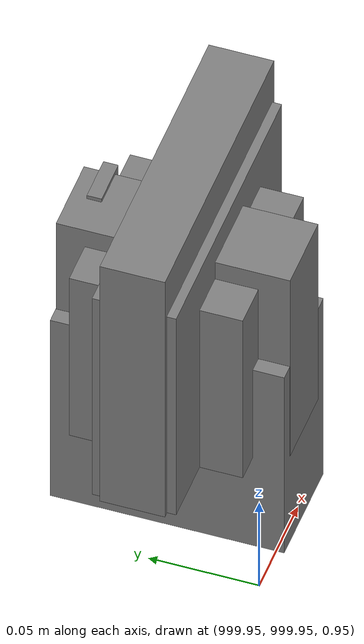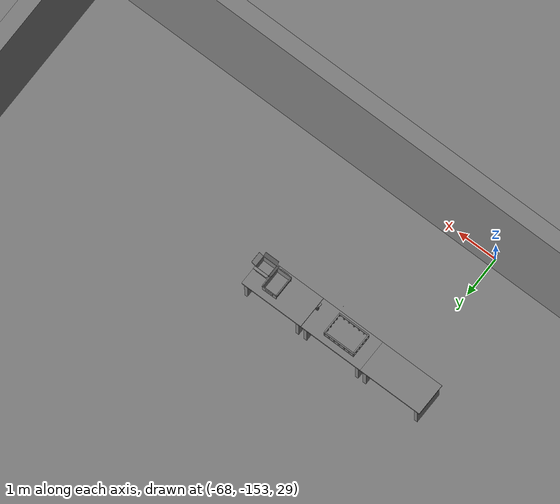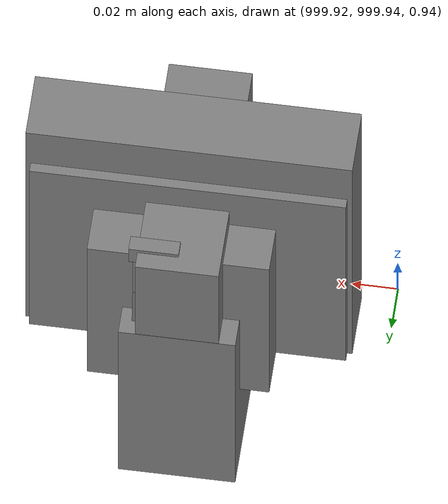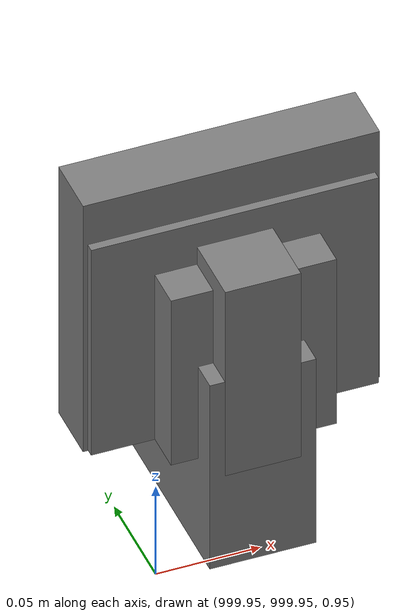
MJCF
<mujoco>
    <option gravity="0.000000000 0.000000000 -9.810000420" timestep="0.0049999999" integrator="implicitfast" density="1.225" viscosity="1.8000001e-05" noslip_iterations="10" iterations="100" sdf_iterations="50">
        <flag multiccd="disable"/>
    </option>
    <size memory="1000M"/>
    <compiler coordinate="local"/>
    <worldbody>
        <light cutoff="30" pos="0 1 1" dir="0 -1 -2"/>
        <light cutoff="30" pos="0 -1 1" dir="0 1 -2"/>
        <body pos="1000.000000000 1000.000000000 1.000000000" euler="0.000000000 0.000000000 180.000000000" name="openloong_gripper_2f85_fix_base_usda_battery_01">
            <geom contype="1" conaffinity="1" density="1000" type="box" material="" rgba="0.500000000 0.500000000 0.500000000 1.000000000" solimp="0.899999976 0.949999988 0.001000000" friction="1.000000000 0.005000000 0.000100000" solref="0.020000000 1.000000000" margin="0" condim="3" group="0" pos="-0.011123657 -0.041940309 0.101691343" quat="1.000000000 0.000000000 0.000000000 0.000000000" size="0.010800000 0.003375000 0.004725000" name="openloong_gripper_2f85_fix_base_usda_geom_B1D86B3E_8C28_4CFF_A8B7_1A2282837219"/>
            <geom contype="1" conaffinity="1" density="1000" type="box" material="" rgba="0.500000000 0.500000000 0.500000000 1.000000000" solimp="0.899999976 0.949999988 0.001000000" friction="1.000000000 0.005000000 0.000100000" solref="0.020000000 1.000000000" margin="0" condim="3" group="0" pos="-0.010876465 -0.044247437 0.047066893" quat="0.998702705 -0.050920475 0.000000000 0.000000000" size="0.009450001 0.002700000 0.024975000" name="openloong_gripper_2f85_fix_base_usda_geom_17B2CF28_A039_45AF_A989_5A1B40308223"/>
            <geom contype="1" conaffinity="1" density="1000" type="box" material="" rgba="0.500000000 0.500000000 0.500000000 1.000000000" solimp="0.899999976 0.949999988 0.001000000" friction="1.000000000 0.005000000 0.000100000" solref="0.020000000 1.000000000" margin="0" condim="3" group="0" pos="-0.001235962 -0.000659180 0.047381196" quat="1.000000000 0.000000000 0.000000000 0.000000000" size="0.039420001 0.039150000 0.047250003" name="openloong_gripper_2f85_fix_base_usda_geom_6245B70F_0955_43B5_A01F_F96B3ECD9327"/>
            <geom contype="1" conaffinity="1" density="1000" type="box" material="" rgba="0.500000000 0.500000000 0.500000000 1.000000000" solimp="0.899999976 0.949999988 0.001000000" friction="1.000000000 0.005000000 0.000100000" solref="0.020000000 1.000000000" margin="0" condim="3" group="0" pos="-0.010876465 -0.039138794 0.009851727" quat="1.000000000 0.000000000 0.000000000 0.000000000" size="0.009450001 0.010800000 0.013500000" name="openloong_gripper_2f85_fix_base_usda_geom_F7516216_A0CD_4E0A_AE7F_3B0930FE543E"/>
            <geom contype="1" conaffinity="1" density="1000" type="box" material="" rgba="0.500000000 0.500000000 0.500000000 1.000000000" solimp="0.899999976 0.949999988 0.001000000" friction="1.000000000 0.005000000 0.000100000" solref="0.020000000 1.000000000" margin="0" condim="3" group="0" pos="-0.010876465 -0.041528322 0.071508206" quat="1.000000000 0.000000000 0.000000000 0.000000000" size="0.009450001 0.002700000 0.027000001" name="openloong_gripper_2f85_fix_base_usda_geom_B1DB4305_6C5C_4FCF_B156_55AB9302EF67"/>
            <freejoint name="openloong_gripper_2f85_fix_base_usda_battery_01_joint"/>
            <site size="0.005000000 0.005000000 0.005000000" rgba="0.500000000 0.500000000 0.500000000 1.000000000" pos="0.000000000 0.000000000 0.000000000" quat="0.999961913 0.008726500 0.000000000 0.000000000" group="0" type="sphere" name="openloong_gripper_2f85_fix_base_usda_battery_01site"/>
        </body>
        <body pos="-66.067138672 -149.164123535 31.167146683" euler="-130.308456421 -89.315536499 42.209957123" mocap="true" name="spotlight3_SpotLight"/>
        <body pos="1000.000000000 1000.000000000 1.000000000" euler="0.000000000 0.000000000 180.000000000" name="openloong_gripper_2f85_fix_base_usda_wifi_box">
            <geom contype="1" conaffinity="1" density="1000" type="box" material="" rgba="0.500000000 0.500000000 0.500000000 1.000000000" solimp="0.899999976 0.949999988 0.001000000" friction="1.000000000 0.005000000 0.000100000" solref="0.020000000 1.000000000" margin="0" condim="3" group="0" pos="0.000000000 0.000000000 0.058978677" quat="0.000000000 0.000000047 0.000000000 1.000000000" size="0.068499997 0.018999999 0.059000000" name="openloong_gripper_2f85_fix_base_usda_geom_6B5B1251_8027_440D_A2D8_C9648351C786"/>
            <freejoint name="openloong_gripper_2f85_fix_base_usda_wifi_box_joint"/>
            <site size="0.005000000 0.005000000 0.005000000" rgba="0.500000000 0.500000000 0.500000000 1.000000000" pos="0.000000000 0.000000000 0.000000000" quat="0.999961913 0.008726500 0.000000000 0.000000000" group="0" type="sphere" name="openloong_gripper_2f85_fix_base_usda_wifi_boxsite"/>
        </body>
        <body pos="1000.000000000 999.999938965 1.000000000" euler="0.000000000 0.000000000 180.000000000" name="openloong_gripper_2f85_fix_base_usda_intelcore_i5">
            <geom contype="1" conaffinity="1" density="1000" type="box" material="" rgba="0.500000000 0.500000000 0.500000000 1.000000000" solimp="0.899999976 0.949999988 0.001000000" friction="1.000000000 0.005000000 0.000100000" solref="0.020000000 1.000000000" margin="0" condim="3" group="0" pos="0.000000000 0.000000000 0.051722717" quat="0.707106709 0.000000000 0.000000000 -0.707106769" size="0.052800000 0.018080002 0.052800000" name="openloong_gripper_2f85_fix_base_usda_geom_77A592B7_2C7C_4E4A_8663_02C90CE29CE4"/>
            <freejoint name="openloong_gripper_2f85_fix_base_usda_intelcore_i5_joint"/>
            <site size="0.005000000 0.005000000 0.005000000" rgba="0.500000000 0.500000000 0.500000000 1.000000000" pos="0.000000000 0.000000000 0.000000000" quat="0.999961913 0.008726534 0.000000000 0.000000000" group="0" type="sphere" name="openloong_gripper_2f85_fix_base_usda_intelcore_i5site"/>
        </body>
        <body pos="-66.051910400 -149.466842651 31.165340424" euler="4.366511345 62.926563263 -85.763359070" mocap="true" name="spotlight5_SpotLight"/>
        <body pos="1000.000000000 1000.000000000 1.000000000" euler="0.000011953 0.000005123 -179.999984741" name="openloong_gripper_2f85_fix_base_usda_intel_box">
            <geom contype="1" conaffinity="1" density="1000" type="box" material="" rgba="0.500000000 0.500000000 0.500000000 1.000000000" solimp="0.899999976 0.949999988 0.001000000" friction="1.000000000 0.005000000 0.000100000" solref="0.020000000 1.000000000" margin="0" condim="3" group="0" pos="0.000000000 -0.000067139 0.000082284" quat="0.707106709 0.000000225 0.000000253 0.707106650" size="0.052800003 0.025300000 0.052800003" name="openloong_gripper_2f85_fix_base_usda_geom_44E42000_570E_455D_9C46_7E13F8596D5A"/>
            <freejoint name="openloong_gripper_2f85_fix_base_usda_intel_box_joint"/>
            <site size="0.005000000 0.005000000 0.005000000" rgba="0.500000000 0.500000000 0.500000000 1.000000000" pos="0.000000000 0.000000000 0.000000000" quat="0.999961913 0.008726500 0.000000000 0.000000000" group="0" type="sphere" name="openloong_gripper_2f85_fix_base_usda_intel_boxsite"/>
        </body>
        <body pos="1000.000000000 1000.000000000 1.000000000" euler="0.000000000 0.000000000 180.000000000" name="openloong_gripper_2f85_fix_base_usda_cpu_fan">
            <geom contype="1" conaffinity="1" density="1000" type="box" material="" rgba="0.500000000 0.500000000 0.500000000 1.000000000" solimp="0.899999976 0.949999988 0.001000000" friction="1.000000000 0.005000000 0.000100000" solref="0.020000000 1.000000000" margin="0" condim="3" group="0" pos="0.000000000 0.000000000 0.070034981" quat="0.000000000 0.000000000 0.000000000 1.000000000" size="0.070700005 0.014699999 0.070700005" name="openloong_gripper_2f85_fix_base_usda_geom_DB3E4EE9_B89C_4758_8388_326A132A27BF"/>
            <freejoint name="openloong_gripper_2f85_fix_base_usda_cpu_fan_joint"/>
            <site size="0.005000000 0.005000000 0.005000000" rgba="0.500000000 0.500000000 0.500000000 1.000000000" pos="0.000000000 0.000000000 0.000000000" quat="0.999961913 0.008726535 0.000000000 0.000000000" group="0" type="sphere" name="openloong_gripper_2f85_fix_base_usda_cpu_fancsite"/>
        </body>
        <body pos="-66.261207581 -149.559555054 31.167053223" euler="81.890274048 46.593135834 16.054588318" mocap="true" name="spotlight4_SpotLight"/>
        <body pos="-64.866622925 -149.383972168 30.183746338" euler="89.999984741 89.999946594 0.000000000" name="openloong_gripper_2f85_fix_base_usda_bluebox_01">
            <geom contype="1" conaffinity="1" density="1000" type="box" material="" rgba="0.500000000 0.500000000 0.500000000 1.000000000" solimp="0.899999976 0.949999988 0.001000000" friction="1.000000000 0.005000000 0.000100000" solref="0.020000000 1.000000000" margin="0" condim="3" group="0" pos="0.276580811 0.187225342 0.000068665" quat="0.707106948 0.000077471 0.707106352 0.000077486" size="0.100000001 0.057999998 0.010000000" name="openloong_gripper_2f85_fix_base_usda_geom_6A07710B_D272_4EDB_8CFB_F398C9E7C39A"/>
            <geom contype="1" conaffinity="1" density="1000" type="box" material="" rgba="0.500000000 0.500000000 0.500000000 1.000000000" solimp="0.899999976 0.949999988 0.001000000" friction="1.000000000 0.005000000 0.000100000" solref="0.020000000 1.000000000" margin="0" condim="3" group="0" pos="0.000000000 0.002883911 0.000000000" quat="0.999999881 0.000000000 0.000000000 0.000000000" size="0.254000008 0.003000000 0.172000006" name="openloong_gripper_2f85_fix_base_usda_geom_B6D8DCD2_CDAB_4878_A16D_1B6756206D53"/>
            <geom contype="1" conaffinity="1" density="1000" type="box" material="" rgba="0.500000000 0.500000000 0.500000000 1.000000000" solimp="0.899999976 0.949999988 0.001000000" friction="1.000000000 0.005000000 0.000100000" solref="0.020000000 1.000000000" margin="0" condim="3" group="0" pos="0.000000000 0.124874115 0.173484802" quat="0.999796331 0.020176515 -0.000000015 0.000000030" size="0.259999990 0.119999997 0.007000000" name="openloong_gripper_2f85_fix_base_usda_geom_7AD7B4BA_8AA2_403A_AC26_C0ED77EA1E6D"/>
            <geom contype="1" conaffinity="1" density="1000" type="box" material="" rgba="0.500000000 0.500000000 0.500000000 1.000000000" solimp="0.899999976 0.949999988 0.001000000" friction="1.000000000 0.005000000 0.000100000" solref="0.020000000 1.000000000" margin="0" condim="3" group="0" pos="0.000000000 0.124874115 -0.173469543" quat="0.999796331 -0.020176545 -0.000000015 0.000000000" size="0.259999990 0.119999997 0.007000000" name="openloong_gripper_2f85_fix_base_usda_geom_B22A9A4C_992E_4D7B_965E_BA58D7FB4CF8"/>
            <geom contype="1" conaffinity="1" density="1000" type="box" material="" rgba="0.500000000 0.500000000 0.500000000 1.000000000" solimp="0.899999976 0.949999988 0.001000000" friction="1.000000000 0.005000000 0.000100000" solref="0.020000000 1.000000000" margin="0" condim="3" group="0" pos="0.000000000 0.214008331 0.188980103" quat="0.999912977 0.013176724 0.000000015 0.000000000" size="0.259999990 0.029999999 0.012500000" name="openloong_gripper_2f85_fix_base_usda_geom_9B562894_0113_4416_9FBA_D7CF7352DCA8"/>
            <geom contype="1" conaffinity="1" density="1000" type="box" material="" rgba="0.500000000 0.500000000 0.500000000 1.000000000" solimp="0.899999976 0.949999988 0.001000000" friction="1.000000000 0.005000000 0.000100000" solref="0.020000000 1.000000000" margin="0" condim="3" group="0" pos="-0.258361816 0.125289917 0.001876831" quat="0.702796936 -0.020792112 0.710783124 0.020769298" size="0.189999998 0.119999997 0.009000000" name="openloong_gripper_2f85_fix_base_usda_geom_1062E372_DC4B_4707_8D82_F7D1994BC808"/>
            <geom contype="1" conaffinity="1" density="1000" type="box" material="" rgba="0.500000000 0.500000000 0.500000000 1.000000000" solimp="0.899999976 0.949999988 0.001000000" friction="1.000000000 0.005000000 0.000100000" solref="0.020000000 1.000000000" margin="0" condim="3" group="0" pos="0.000000000 0.214008331 -0.188980103" quat="0.999912977 -0.013176769 0.000000030 0.000000015" size="0.259999990 0.029999999 0.012500000" name="openloong_gripper_2f85_fix_base_usda_geom_69E1F382_7C42_4BFC_876C_5AAB02CE0054"/>
            <geom contype="1" conaffinity="1" density="1000" type="box" material="" rgba="0.500000000 0.500000000 0.500000000 1.000000000" solimp="0.899999976 0.949999988 0.001000000" friction="1.000000000 0.005000000 0.000100000" solref="0.020000000 1.000000000" margin="0" condim="3" group="0" pos="-0.276611328 0.187225342 0.000068665" quat="0.707106650 0.000077441 0.707106709 0.000077456" size="0.100000001 0.057999998 0.010000000" name="openloong_gripper_2f85_fix_base_usda_geom_5D2CE6B0_03FA_4F5A_87D0_C5B17A24AEC1"/>
            <geom contype="1" conaffinity="1" density="1000" type="box" material="" rgba="0.500000000 0.500000000 0.500000000 1.000000000" solimp="0.899999976 0.949999988 0.001000000" friction="1.000000000 0.005000000 0.000100000" solref="0.020000000 1.000000000" margin="0" condim="3" group="0" pos="0.258331299 0.125289917 0.001876831" quat="0.702851415 0.018856421 0.710823774 -0.019329369" size="0.189999998 0.119999997 0.009000000" name="openloong_gripper_2f85_fix_base_usda_geom_9279F4B0_8A2A_46A1_9D21_3DFAD6F63102"/>
            <freejoint name="openloong_gripper_2f85_fix_base_usda_bluebox_01_joint"/>
            <site size="0.005000000 0.005000000 0.005000000" rgba="0.500000000 0.500000000 0.500000000 1.000000000" pos="0.000000000 0.000000000 0.000000000" quat="0.999961913 0.008726534 0.000000000 0.000000000" group="0" type="sphere" name="openloong_gripper_2f85_fix_base_usda_bluebox_01site"/>
        </body>
        <body pos="-64.496299744 -149.491867065 30.235729218" euler="0.000000000 0.000000000 89.999946594" name="openloong_gripper_2f85_fix_base_usda_cardboardbox_01">
            <geom contype="1" conaffinity="1" density="1000" type="box" material="" rgba="0.500000000 0.500000000 0.500000000 1.000000000" solimp="0.899999976 0.949999988 0.001000000" friction="1.000000000 0.005000000 0.000100000" solref="0.020000000 1.000000000" margin="0" condim="3" group="0" pos="-0.003166199 -0.004086494 0.005052090" quat="1.000000000 0.000000000 0.000000000 0.000000000" size="0.142499998 0.177500010 0.005000000" name="openloong_gripper_2f85_fix_base_usda_geom_041E8E98_2869_44AE_8507_0A0C8A63D822"/>
            <geom contype="1" conaffinity="1" density="1000" type="box" material="" rgba="0.500000000 0.500000000 0.500000000 1.000000000" solimp="0.899999976 0.949999988 0.001000000" friction="1.000000000 0.005000000 0.000100000" solref="0.020000000 1.000000000" margin="0" condim="3" group="0" pos="-0.003166199 0.170316696 0.150570869" quat="1.000000000 0.000000000 0.000000000 0.000000000" size="0.142499998 0.005000000 0.149999991" name="openloong_gripper_2f85_fix_base_usda_geom_35B79C12_E1AF_42C6_88A0_620FC1735C6F"/>
            <geom contype="1" conaffinity="1" density="1000" type="box" material="" rgba="0.500000000 0.500000000 0.500000000 1.000000000" solimp="0.899999976 0.949999988 0.001000000" friction="1.000000000 0.005000000 0.000100000" solref="0.020000000 1.000000000" margin="0" condim="3" group="0" pos="-0.147399902 -0.005307198 0.150570869" quat="1.000000000 0.000000000 0.000000000 0.000000000" size="0.005000000 0.177500010 0.149999991" name="openloong_gripper_2f85_fix_base_usda_geom_D3D32301_1BD2_45E8_9DC4_8DD55C140AAE"/>
            <geom contype="1" conaffinity="1" density="1000" type="box" material="" rgba="0.500000000 0.500000000 0.500000000 1.000000000" solimp="0.899999976 0.949999988 0.001000000" friction="1.000000000 0.005000000 0.000100000" solref="0.020000000 1.000000000" margin="0" condim="3" group="0" pos="0.140275955 -0.005307198 0.150570869" quat="1.000000000 0.000000000 0.000000000 0.000000000" size="0.005000000 0.177500010 0.149999991" name="openloong_gripper_2f85_fix_base_usda_geom_5CDEE442_1C06_4C31_A539_A9BFD803E583"/>
            <geom contype="1" conaffinity="1" density="1000" type="box" material="" rgba="0.500000000 0.500000000 0.500000000 1.000000000" solimp="0.899999976 0.949999988 0.001000000" friction="1.000000000 0.005000000 0.000100000" solref="0.020000000 1.000000000" margin="0" condim="3" group="0" pos="-0.003166199 -0.181550980 0.150570869" quat="1.000000000 0.000000000 0.000000000 0.000000000" size="0.142499998 0.005000000 0.149999991" name="openloong_gripper_2f85_fix_base_usda_geom_80334359_632E_4704_8A44_FD0012CFACDB"/>
            <freejoint name="openloong_gripper_2f85_fix_base_usda_cardboardbox_01_joint"/>
            <site size="0.005000000 0.005000000 0.005000000" rgba="0.500000000 0.500000000 0.500000000 1.000000000" pos="0.000000000 0.000000000 0.000000000" quat="0.999961913 0.008726535 0.000000000 0.000000000" group="0" type="sphere" name="openloong_gripper_2f85_fix_base_usda_site_84008B06_5EF1_42D4_AE8E_4513B0270FA1"/>
            <body pos="0.139160156 -0.004048347 0.301930904" euler="-179.999954224 49.383502960 179.999954224" name="openloong_gripper_2f85_fix_base_usda_A1_006">
                <geom contype="1" conaffinity="1" density="1000" type="box" material="" rgba="0.500000000 0.500000000 0.500000000 1.000000000" solimp="0.899999976 0.949999988 0.001000000" friction="1.000000000 0.005000000 0.000100000" solref="0.020000000 1.000000000" margin="0" condim="3" group="0" pos="-0.071587563 0.000009537 0.001745224" quat="0.999999881 0.000000000 0.000000000 0.000000000" size="0.071249999 0.179999992 0.002500000" name="openloong_gripper_2f85_fix_base_usda_geom_07277F09_9797_4831_9D7E_1C6E08CF98FD"/>
                <joint armature="0" stiffness="0.07" damping="0.0099999998" axis="0.000000 1.000000 0.000000" type="hinge" name="openloong_gripper_2f85_fix_base_usda_A1_006"/>
            </body>
            <body pos="-0.145902634 -0.004086494 0.301938057" euler="-180.000000000 -60.000011444 -180.000000000" name="openloong_gripper_2f85_fix_base_usda_A2_006">
                <geom contype="1" conaffinity="1" density="1000" type="box" material="" rgba="0.500000000 0.500000000 0.500000000 1.000000000" solimp="0.899999976 0.949999988 0.001000000" friction="1.000000000 0.005000000 0.000100000" solref="0.020000000 1.000000000" margin="0" condim="3" group="0" pos="0.071268082 0.000009537 0.002717972" quat="0.000002921 0.000000000 -0.000000030 0.999999881" size="0.071249999 0.179999992 0.002500000" name="openloong_gripper_2f85_fix_base_usda_geom_B43E87E8_ACDA_4657_A8D5_30175288487F"/>
                <joint armature="0" stiffness="0.07" damping="0.0099999998" axis="0.000000 1.000000 0.000000" type="hinge" name="openloong_gripper_2f85_fix_base_usda_A2_006"/>
            </body>
            <body pos="-0.003385544 0.175991058 0.301930904" euler="-125.858116150 -0.000004561 0.000002331" name="openloong_gripper_2f85_fix_base_usda_B2_006">
                <geom contype="1" conaffinity="1" density="1000" type="box" material="" rgba="0.500000000 0.500000000 0.500000000 1.000000000" solimp="0.899999976 0.949999988 0.001000000" friction="1.000000000 0.005000000 0.000100000" solref="0.020000000 1.000000000" margin="0" condim="3" group="0" pos="0.000009537 -0.070939064 -0.002470016" quat="0.999614120 0.027776197 -0.000000015 0.000000030" size="0.137500003 0.064999998 0.005000000" name="openloong_gripper_2f85_fix_base_usda_geom_82F27FE2_DA72_4AE2_BD85_A742538A153B"/>
                <joint armature="0" stiffness="0.07" damping="0.0099999998" axis="1.000000 0.000000 0.000000" type="hinge" name="openloong_gripper_2f85_fix_base_usda_B2_006"/>
            </body>
            <body pos="-0.003385544 -0.184140205 0.301938057" euler="147.805557251 0.000000000 0.000000000" name="openloong_gripper_2f85_fix_base_usda_B1_006">
                <geom contype="1" conaffinity="1" density="1000" type="box" material="" rgba="0.500000000 0.500000000 0.500000000 1.000000000" solimp="0.899999976 0.949999988 0.001000000" friction="1.000000000 0.005000000 0.000100000" solref="0.020000000 1.000000000" margin="0" condim="3" group="0" pos="-0.000028610 0.070202351 -0.002703667" quat="0.999614179 -0.027776167 0.000000000 0.000000000" size="0.137500003 0.064999998 0.005000000" name="openloong_gripper_2f85_fix_base_usda_geom_10E2AEF4_3748_473F_ACA7_3D680C7CF8E9"/>
                <joint armature="0" stiffness="0.07" damping="0.0099999998" axis="1.000000 0.000000 0.000000" type="hinge" name="openloong_gripper_2f85_fix_base_usda_B1_006"/>
            </body>
        </body>
        <body pos="-65.882858276 -149.481979370 30.229999542" euler="-64.487716675 0.000000000 0.000000000" name="openloong_gripper_2f85_fix_base_usda_Barcode">
            <geom contype="1" conaffinity="1" density="1000" type="box" material="" rgba="0.500000000 0.500000000 0.500000000 1.000000000" solimp="0.899999976 0.949999988 0.001000000" friction="1.000000000 0.005000000 0.000100000" solref="0.020000000 1.000000000" margin="0" condim="3" group="0" pos="0.000000000 0.013038635 0.001419067" quat="0.000000000 0.000000000 0.000000000 1.000000119" size="0.034000002 0.010000000 0.017999999" name="openloong_gripper_2f85_fix_base_usda_geom_CAF9027D_CF2D_4924_B3F8_67E0BCD587AF"/>
            <geom contype="1" conaffinity="1" density="1000" type="box" material="" rgba="0.500000000 0.500000000 0.500000000 1.000000000" solimp="0.899999976 0.949999988 0.001000000" friction="1.000000000 0.005000000 0.000100000" solref="0.020000000 1.000000000" margin="0" condim="3" group="0" pos="0.000000000 -0.035301208 -0.007095337" quat="0.000000000 0.000000000 -0.043619365 0.999048233" size="0.028999999 0.010000000 0.020000000" name="openloong_gripper_2f85_fix_base_usda_geom_575ADD5D_CA02_41D3_A81F_D037EE7BF138"/>
            <geom contype="1" conaffinity="1" density="1000" type="box" material="" rgba="0.500000000 0.500000000 0.500000000 1.000000000" solimp="0.899999976 0.949999988 0.001000000" friction="1.000000000 0.005000000 0.000100000" solref="0.020000000 1.000000000" margin="0" condim="3" group="0" pos="0.000000000 -0.043411255 -0.011749268" quat="0.922262907 0.386563420 0.000000000 0.000000000" size="0.026000001 0.010000000 0.020000000" name="openloong_gripper_2f85_fix_base_usda_geom_B5215651_2B86_419B_865B_2443AB8CE2D5"/>
            <geom contype="1" conaffinity="1" density="1000" type="box" material="" rgba="0.500000000 0.500000000 0.500000000 1.000000000" solimp="0.899999976 0.949999988 0.001000000" friction="1.000000000 0.005000000 0.000100000" solref="0.020000000 1.000000000" margin="0" condim="3" group="0" pos="0.000000000 -0.016967773 -0.031860352" quat="0.000000000 0.000000000 0.000000000 1.000000119" size="0.008000000 0.010000000 0.013000000" name="openloong_gripper_2f85_fix_base_usda_geom_F2E790A7_9AE6_43F6_91E7_0780AC3AC909"/>
            <geom contype="1" conaffinity="1" density="1000" type="box" material="" rgba="0.500000000 0.500000000 0.500000000 1.000000000" solimp="0.899999976 0.949999988 0.001000000" friction="1.000000000 0.005000000 0.000100000" solref="0.020000000 1.000000000" margin="0" condim="3" group="0" pos="0.000000000 -0.001869202 0.000312805" quat="0.953716993 0.300705761 0.000000000 0.000000000" size="0.032000002 0.010000000 0.018999999" name="openloong_gripper_2f85_fix_base_usda_geom_6E8139B9_D1C0_4C8F_AE30_BC04EA35FD4F"/>
            <geom contype="1" conaffinity="1" density="1000" type="box" material="" rgba="0.500000000 0.500000000 0.500000000 1.000000000" solimp="0.899999976 0.949999988 0.001000000" friction="1.000000000 0.005000000 0.000100000" solref="0.020000000 1.000000000" margin="0" condim="3" group="0" pos="0.000000000 -0.019531250 -0.003173828" quat="0.953716993 0.300705761 0.000000000 0.000000000" size="0.030999999 0.010000000 0.020000000" name="openloong_gripper_2f85_fix_base_usda_geom_4F47CF3E_7038_449B_B083_A30029EDB046"/>
            <geom contype="1" conaffinity="1" density="1000" type="box" material="" rgba="0.500000000 0.500000000 0.500000000 1.000000000" solimp="0.899999976 0.949999988 0.001000000" friction="1.000000000 0.005000000 0.000100000" solref="0.020000000 1.000000000" margin="0" condim="3" group="0" pos="0.000000000 -0.035301208 -0.007095337" quat="0.953716993 0.300705761 0.000000000 0.000000000" size="0.028999999 0.010000000 0.020000000" name="openloong_gripper_2f85_fix_base_usda_geom_BF1CA0D3_ECE4_42DA_B9CC_05E4C536239C"/>
            <geom contype="1" conaffinity="1" density="1000" type="box" material="" rgba="0.500000000 0.500000000 0.500000000 1.000000000" solimp="0.899999976 0.949999988 0.001000000" friction="1.000000000 0.005000000 0.000100000" solref="0.020000000 1.000000000" margin="0" condim="3" group="0" pos="0.000000000 -0.042617798 -0.071121216" quat="0.000000000 0.000000000 0.000000000 1.000000119" size="0.013000000 0.021000000 0.059999999" name="openloong_gripper_2f85_fix_base_usda_geom_0BDC28C2_18F9_4B35_9A62_27F611DA76EC"/>
            <freejoint name="openloong_gripper_2f85_fix_base_usda_Barcode_joint"/>
            <site size="0.005000000 0.005000000 0.005000000" rgba="0.500000000 0.500000000 0.500000000 1.000000000" pos="0.000000000 0.000000000 0.000000000" quat="1.000000000 0.000000000 0.000000000 0.000000000" group="0" type="sphere" name="openloong_gripper_2f85_fix_base_usda_Barcode_site"/>
        </body>
        <body pos="-66.745018005 -149.392349243 30.184000015" euler="0.000000000 0.000000000 89.999946594" name="[22330269833585]_Basket_01">
            <geom contype="1" conaffinity="1" density="1000" type="box" material="" rgba="0.500000000 0.500000000 0.500000000 1.000000000" solimp="0.899999976 0.949999988 0.001000000" friction="1.000000000 0.005000000 0.000100000" solref="0.020000000 1.000000000" margin="0" condim="3" group="0" pos="-0.052425385 0.389207840 0.089787483" quat="0.707107008 0.000000000 0.000000000 0.707106411" size="0.014249999 0.014249999 0.059999999" name="[22330269833585]_geom_4C98B7D1_6DC0_4B63_B66F_3A8546E878BD"/>
            <geom contype="1" conaffinity="1" density="1000" type="box" material="" rgba="0.500000000 0.500000000 0.500000000 1.000000000" solimp="0.899999976 0.949999988 0.001000000" friction="1.000000000 0.005000000 0.000100000" solref="0.020000000 1.000000000" margin="0" condim="3" group="0" pos="0.264015198 -0.133043289 0.089787483" quat="0.707107008 0.000000000 0.000000000 0.707106411" size="0.014249999 0.014249999 0.059999999" name="[22330269833585]_geom_F698E225_B89A_40AA_A61E_FFB241052FD3"/>
            <geom contype="1" conaffinity="1" density="1000" type="box" material="" rgba="0.500000000 0.500000000 0.500000000 1.000000000" solimp="0.899999976 0.949999988 0.001000000" friction="1.000000000 0.005000000 0.000100000" solref="0.020000000 1.000000000" margin="0" condim="3" group="0" pos="-0.264015198 -0.265548706 0.089793205" quat="0.707107008 0.000000000 0.000000000 0.707106411" size="0.014249999 0.014249999 0.059999999" name="[22330269833585]_geom_6B1322A4_09F2_42CD_AF3F_C5AC39A97AC8"/>
            <geom contype="1" conaffinity="1" density="1000" type="box" material="" rgba="0.500000000 0.500000000 0.500000000 1.000000000" solimp="0.899999976 0.949999988 0.001000000" friction="1.000000000 0.005000000 0.000100000" solref="0.020000000 1.000000000" margin="0" condim="3" group="0" pos="-0.160263062 -0.389322281 0.089793205" quat="0.707107008 0.000000000 0.000000000 0.707106411" size="0.014249999 0.014249999 0.059999999" name="[22330269833585]_geom_86A0D612_82DD_4C5F_9B13_59B65BEAEC76"/>
            <geom contype="1" conaffinity="1" density="1000" type="box" material="" rgba="0.500000000 0.500000000 0.500000000 1.000000000" solimp="0.899999976 0.949999988 0.001000000" friction="1.000000000 0.005000000 0.000100000" solref="0.020000000 1.000000000" margin="0" condim="3" group="0" pos="0.162265778 -0.389322281 0.089787483" quat="0.707107008 0.000000000 0.000000000 0.707106411" size="0.014249999 0.014249999 0.059999999" name="[22330269833585]_geom_78357505_6936_4241_A57D_FB0D1879F577"/>
            <geom contype="1" conaffinity="1" density="1000" type="box" material="" rgba="0.500000000 0.500000000 0.500000000 1.000000000" solimp="0.899999976 0.949999988 0.001000000" friction="1.000000000 0.005000000 0.000100000" solref="0.020000000 1.000000000" margin="0" condim="3" group="0" pos="0.264015198 0.389207840 0.089787483" quat="0.707107008 0.000000000 0.000000000 0.707106411" size="0.014249999 0.014249999 0.059999999" name="[22330269833585]_geom_BDAA1972_0140_4F15_A324_691BBBD891AE"/>
            <geom contype="1" conaffinity="1" density="1000" type="box" material="" rgba="0.500000000 0.500000000 0.500000000 1.000000000" solimp="0.899999976 0.949999988 0.001000000" friction="1.000000000 0.005000000 0.000100000" solref="0.020000000 1.000000000" margin="0" condim="3" group="0" pos="-0.264015198 -0.133043289 0.089793205" quat="0.707107008 0.000000000 0.000000000 0.707106411" size="0.014249999 0.014249999 0.059999999" name="[22330269833585]_geom_F8759CD1_C9A5_4E3A_94F8_49CCC1068184"/>
            <geom contype="1" conaffinity="1" density="1000" type="box" material="" rgba="0.500000000 0.500000000 0.500000000 1.000000000" solimp="0.899999976 0.949999988 0.001000000" friction="1.000000000 0.005000000 0.000100000" solref="0.020000000 1.000000000" margin="0" condim="3" group="0" pos="-0.264026642 0.269256592 0.089793205" quat="0.707107008 0.000000000 0.000000000 0.707106411" size="0.014249999 0.014249999 0.059999999" name="[22330269833585]_geom_B50AA665_8277_42E5_9E5B_B09960661788"/>
            <geom contype="1" conaffinity="1" density="1000" type="box" material="" rgba="0.500000000 0.500000000 0.500000000 1.000000000" solimp="0.899999976 0.949999988 0.001000000" friction="1.000000000 0.005000000 0.000100000" solref="0.020000000 1.000000000" margin="0" condim="3" group="0" pos="0.054462433 0.389207840 0.089787483" quat="0.707107008 0.000000000 0.000000000 0.707106411" size="0.014249999 0.014249999 0.059999999" name="[22330269833585]_geom_13A6608A_7077_4D6A_BAC0_5665F21F576A"/>
            <geom contype="1" conaffinity="1" density="1000" type="box" material="" rgba="0.500000000 0.500000000 0.500000000 1.000000000" solimp="0.899999976 0.949999988 0.001000000" friction="1.000000000 0.005000000 0.000100000" solref="0.020000000 1.000000000" margin="0" condim="3" group="0" pos="0.054462433 -0.389322281 0.089787483" quat="0.707107008 0.000000000 0.000000000 0.707106411" size="0.014249999 0.014249999 0.059999999" name="[22330269833585]_geom_B27530B4_621D_44F8_9A37_2DECE6BF9D28"/>
            <geom contype="1" conaffinity="1" density="1000" type="box" material="" rgba="0.500000000 0.500000000 0.500000000 1.000000000" solimp="0.899999976 0.949999988 0.001000000" friction="1.000000000 0.005000000 0.000100000" solref="0.020000000 1.000000000" margin="0" condim="3" group="0" pos="0.264015198 0.269256592 0.089793205" quat="0.707107008 0.000000000 0.000000000 0.707106411" size="0.014249999 0.014249999 0.059999999" name="[22330269833585]_geom_35DD3954_1CAD_41C2_B886_030BE2192223"/>
            <geom contype="1" conaffinity="1" density="1000" type="box" material="" rgba="0.500000000 0.500000000 0.500000000 1.000000000" solimp="0.899999976 0.949999988 0.001000000" friction="1.000000000 0.005000000 0.000100000" solref="0.020000000 1.000000000" margin="0" condim="3" group="0" pos="0.264015198 -0.389322281 0.089787483" quat="0.707107008 0.000000000 0.000000000 0.707106411" size="0.014249999 0.014249999 0.059999999" name="[22330269833585]_geom_3058BF91_531B_44E5_8A7A_4607F615542D"/>
            <geom contype="1" conaffinity="1" density="1000" type="box" material="" rgba="0.500000000 0.500000000 0.500000000 1.000000000" solimp="0.899999976 0.949999988 0.001000000" friction="1.000000000 0.005000000 0.000100000" solref="0.020000000 1.000000000" margin="0" condim="3" group="0" pos="0.000000000 0.000000000 0.015998840" quat="0.707107008 0.000000000 0.000000000 0.707106411" size="0.403499991 0.279000014 0.015750000" name="[22330269833585]_geom_92913950_92D4_4646_845D_3B019B0A670C"/>
            <geom contype="1" conaffinity="1" density="1000" type="box" material="" rgba="0.500000000 0.500000000 0.500000000 1.000000000" solimp="0.899999976 0.949999988 0.001000000" friction="1.000000000 0.005000000 0.000100000" solref="0.020000000 1.000000000" margin="0" condim="3" group="0" pos="0.000000000 -0.389476776 0.163619041" quat="0.707107008 0.000000000 0.000000000 0.707106411" size="0.015000000 0.277500004 0.015750000" name="[22330269833585]_geom_6AECE764_91F4_4E1C_A20C_8F5CFAF8DD85"/>
            <geom contype="1" conaffinity="1" density="1000" type="box" material="" rgba="0.500000000 0.500000000 0.500000000 1.000000000" solimp="0.899999976 0.949999988 0.001000000" friction="1.000000000 0.005000000 0.000100000" solref="0.020000000 1.000000000" margin="0" condim="3" group="0" pos="0.162265778 0.389207840 0.089787483" quat="0.707107008 0.000000000 0.000000000 0.707106411" size="0.014249999 0.014249999 0.059999999" name="[22330269833585]_geom_A3543BF9_B13A_4255_8958_B62459123A5E"/>
            <geom contype="1" conaffinity="1" density="1000" type="box" material="" rgba="0.500000000 0.500000000 0.500000000 1.000000000" solimp="0.899999976 0.949999988 0.001000000" friction="1.000000000 0.005000000 0.000100000" solref="0.020000000 1.000000000" margin="0" condim="3" group="0" pos="0.000000000 0.389471054 0.163619041" quat="0.707107008 0.000000000 0.000000000 0.707106411" size="0.015000000 0.277500004 0.015750000" name="[22330269833585]_geom_E3AEF540_A024_47B4_9815_2400CFF2661A"/>
            <geom contype="1" conaffinity="1" density="1000" type="box" material="" rgba="0.500000000 0.500000000 0.500000000 1.000000000" solimp="0.899999976 0.949999988 0.001000000" friction="1.000000000 0.005000000 0.000100000" solref="0.020000000 1.000000000" margin="0" condim="3" group="0" pos="-0.263511658 0.000000000 0.163619041" quat="0.707107008 0.000000000 0.000000000 0.707106411" size="0.403499991 0.015000000 0.015750000" name="[22330269833585]_geom_83291F27_1BBA_43B5_BEFF_05F9F55A5616"/>
            <geom contype="1" conaffinity="1" density="1000" type="box" material="" rgba="0.500000000 0.500000000 0.500000000 1.000000000" solimp="0.899999976 0.949999988 0.001000000" friction="1.000000000 0.005000000 0.000100000" solref="0.020000000 1.000000000" margin="0" condim="3" group="0" pos="-0.264015198 0.141334534 0.089793205" quat="0.707107008 0.000000000 0.000000000 0.707106411" size="0.014249999 0.014249999 0.059999999" name="[22330269833585]_geom_777917D1_3516_4408_B9E5_D300228AD480"/>
            <geom contype="1" conaffinity="1" density="1000" type="box" material="" rgba="0.500000000 0.500000000 0.500000000 1.000000000" solimp="0.899999976 0.949999988 0.001000000" friction="1.000000000 0.005000000 0.000100000" solref="0.020000000 1.000000000" margin="0" condim="3" group="0" pos="0.264015198 -0.265548706 0.089787483" quat="0.707107008 0.000000000 0.000000000 0.707106411" size="0.014249999 0.014249999 0.059999999" name="[22330269833585]_geom_FEFA841B_421A_4973_B97F_42F890D81826"/>
            <geom contype="1" conaffinity="1" density="1000" type="box" material="" rgba="0.500000000 0.500000000 0.500000000 1.000000000" solimp="0.899999976 0.949999988 0.001000000" friction="1.000000000 0.005000000 0.000100000" solref="0.020000000 1.000000000" margin="0" condim="3" group="0" pos="-0.160263062 0.389207840 0.089787483" quat="0.707107008 0.000000000 0.000000000 0.707106411" size="0.014249999 0.014249999 0.059999999" name="[22330269833585]_geom_2F9412E2_2C62_4253_9DA3_F87502A79B17"/>
            <geom contype="1" conaffinity="1" density="1000" type="box" material="" rgba="0.500000000 0.500000000 0.500000000 1.000000000" solimp="0.899999976 0.949999988 0.001000000" friction="1.000000000 0.005000000 0.000100000" solref="0.020000000 1.000000000" margin="0" condim="3" group="0" pos="-0.052425385 -0.389322281 0.089787483" quat="0.707107008 0.000000000 0.000000000 0.707106411" size="0.014249999 0.014249999 0.059999999" name="[22330269833585]_geom_D9A69B16_AFBC_4D65_B495_039A8F219D44"/>
            <geom contype="1" conaffinity="1" density="1000" type="box" material="" rgba="0.500000000 0.500000000 0.500000000 1.000000000" solimp="0.899999976 0.949999988 0.001000000" friction="1.000000000 0.005000000 0.000100000" solref="0.020000000 1.000000000" margin="0" condim="3" group="0" pos="-0.264026642 -0.389322281 0.089793205" quat="0.707107008 0.000000000 0.000000000 0.707106411" size="0.014249999 0.014249999 0.059999999" name="[22330269833585]_geom_111B90C7_B272_492C_A4ED_2D687D35785E"/>
            <geom contype="1" conaffinity="1" density="1000" type="box" material="" rgba="0.500000000 0.500000000 0.500000000 1.000000000" solimp="0.899999976 0.949999988 0.001000000" friction="1.000000000 0.005000000 0.000100000" solref="0.020000000 1.000000000" margin="0" condim="3" group="0" pos="0.264015198 0.141334534 0.089787483" quat="0.707107008 0.000000000 0.000000000 0.707106411" size="0.014249999 0.014249999 0.059999999" name="[22330269833585]_geom_A57BF68F_71FC_4F4F_B179_CE7CF06EF29D"/>
            <geom contype="1" conaffinity="1" density="1000" type="box" material="" rgba="0.500000000 0.500000000 0.500000000 1.000000000" solimp="0.899999976 0.949999988 0.001000000" friction="1.000000000 0.005000000 0.000100000" solref="0.020000000 1.000000000" margin="0" condim="3" group="0" pos="-0.264015198 0.389207840 0.089793205" quat="0.707107008 0.000000000 0.000000000 0.707106411" size="0.014249999 0.014249999 0.059999999" name="[22330269833585]_geom_726E61F3_256D_4710_AF19_B74FA0AAE000"/>
            <geom contype="1" conaffinity="1" density="1000" type="box" material="" rgba="0.500000000 0.500000000 0.500000000 1.000000000" solimp="0.899999976 0.949999988 0.001000000" friction="1.000000000 0.005000000 0.000100000" solref="0.020000000 1.000000000" margin="0" condim="3" group="0" pos="0.264015198 0.004480362 0.089787483" quat="0.707107008 0.000000000 0.000000000 0.707106411" size="0.014249999 0.014249999 0.059999999" name="[22330269833585]_geom_CD0FF1FD_8632_4DE0_A2C9_8BD14CD5C94A"/>
            <geom contype="1" conaffinity="1" density="1000" type="box" material="" rgba="0.500000000 0.500000000 0.500000000 1.000000000" solimp="0.899999976 0.949999988 0.001000000" friction="1.000000000 0.005000000 0.000100000" solref="0.020000000 1.000000000" margin="0" condim="3" group="0" pos="0.263694763 -0.000011444 0.163619041" quat="0.707107008 0.000000000 0.000000000 0.707106411" size="0.403499991 0.015000000 0.015750000" name="[22330269833585]_geom_1ED66936_5170_4392_9C52_C3B4CE15091D"/>
            <geom contype="1" conaffinity="1" density="1000" type="box" material="" rgba="0.500000000 0.500000000 0.500000000 1.000000000" solimp="0.899999976 0.949999988 0.001000000" friction="1.000000000 0.005000000 0.000100000" solref="0.020000000 1.000000000" margin="0" condim="3" group="0" pos="-0.264015198 0.004480362 0.089793205" quat="0.707107008 0.000000000 0.000000000 0.707106411" size="0.014249999 0.014249999 0.059999999" name="[22330269833585]_geom_8A1D7D20_A927_44C3_96EE_2D1A9C0B93E7"/>
            <freejoint name="[22330269833585]_joint_F65689EE_5AF7_48EF_A705_CFB969CDFE24"/>
        </body>
        <body pos="0.000000000 0.000000000 0.000000000" euler="0.000000000 0.000000000 0.000000000" name="Static Objects_Static Objects">
            <geom contype="1" conaffinity="1" density="1000" type="box" material="" rgba="0.500000000 0.500000000 0.500000000 1.000000000" solimp="0.899999976 0.949999988 0.001000000" friction="1.000000000 0.005000000 0.000100000" solref="0.020000000 1.000000000" margin="0" condim="3" group="0" pos="-67.544113159 -149.365814209 29.727830887" quat="0.500000417 0.499999970 0.499999553 0.499999970" size="0.381000012 0.319999993 0.041000001" name="Static Objects_geom_E289EEF6_96E6_4B3F_9D9F_0FF78993FAE0"/>
            <geom contype="1" conaffinity="1" density="1000" type="box" material="" rgba="0.500000000 0.500000000 0.500000000 1.000000000" solimp="0.899999976 0.949999988 0.001000000" friction="1.000000000 0.005000000 0.000100000" solref="0.020000000 1.000000000" margin="0" condim="3" group="0" pos="-68.239501953 -149.365814209 30.086868286" quat="0.500000417 0.499999970 0.499999553 0.499999970" size="0.370999992 0.039500002 0.745000005" name="Static Objects_geom_ED9757CC_0933_4740_846A_7C9305FFBF4A"/>
            <geom contype="1" conaffinity="1" density="1000" type="box" material="" rgba="0.500000000 0.500000000 0.500000000 1.000000000" solimp="0.899999976 0.949999988 0.001000000" friction="1.000000000 0.005000000 0.000100000" solref="0.020000000 1.000000000" margin="0" condim="3" group="0" pos="-68.239501953 -149.365814209 30.147235870" quat="0.500000417 0.499999970 0.499999553 0.499999970" size="0.400000006 0.022000000 0.800000012" name="Static Objects_geom_6394ACE8_CE9E_4653_A501_F476FD88F693"/>
            <geom contype="1" conaffinity="1" density="1000" type="box" material="" rgba="0.500000000 0.500000000 0.500000000 1.000000000" solimp="0.899999976 0.949999988 0.001000000" friction="1.000000000 0.005000000 0.000100000" solref="0.020000000 1.000000000" margin="0" condim="3" group="0" pos="-68.934890747 -149.365814209 29.727830887" quat="0.500000417 0.499999970 0.499999553 0.499999970" size="0.381000012 0.319999993 0.041000001" name="Static Objects_geom_CA9587D9_FCD1_43FB_A4C7_B0930840C98A"/>
            <geom contype="1" conaffinity="1" density="1000" type="box" material="" rgba="0.500000000 0.500000000 0.500000000 1.000000000" solimp="0.899999976 0.949999988 0.001000000" friction="1.000000000 0.005000000 0.000100000" solref="0.020000000 1.000000000" margin="0" condim="3" group="0" pos="-68.239501953 -149.365814209 29.561563492" quat="0.500000417 0.499999970 0.499999553 0.499999970" size="0.020000000 0.022000000 0.660000026" name="Static Objects_geom_27D7EDE8_8B70_4409_965D_581BA1DB6AD8"/>
            <geom contype="1" conaffinity="1" density="1000" type="box" material="" rgba="0.500000000 0.500000000 0.500000000 1.000000000" solimp="0.899999976 0.949999988 0.001000000" friction="1.000000000 0.005000000 0.000100000" solref="0.020000000 1.000000000" margin="0" condim="3" group="0" pos="-65.945671082 -149.365814209 29.727830887" quat="0.500000417 0.499999970 0.499999553 0.499999970" size="0.381000012 0.319999993 0.041000001" name="Static Objects_geom_F5CCB712_9D7F_4543_95ED_B554EF6AA12D"/>
            <geom contype="1" conaffinity="1" density="1000" type="box" material="" rgba="0.500000000 0.500000000 0.500000000 1.000000000" solimp="0.899999976 0.949999988 0.001000000" friction="1.000000000 0.005000000 0.000100000" solref="0.020000000 1.000000000" margin="0" condim="3" group="0" pos="-66.641059875 -149.365814209 30.086868286" quat="0.500000417 0.499999970 0.499999553 0.499999970" size="0.370999992 0.039500002 0.745000005" name="Static Objects_geom_74528FB0_CAA8_4451_B124_32BD89C8D2E3"/>
            <geom contype="1" conaffinity="1" density="1000" type="box" material="" rgba="0.500000000 0.500000000 0.500000000 1.000000000" solimp="0.899999976 0.949999988 0.001000000" friction="1.000000000 0.005000000 0.000100000" solref="0.020000000 1.000000000" margin="0" condim="3" group="0" pos="-66.641059875 -149.365814209 30.147235870" quat="0.500000417 0.499999970 0.499999553 0.499999970" size="0.400000006 0.022000000 0.800000012" name="Static Objects_geom_4E295C5F_2CD0_432F_BA3B_A6444B0847B0"/>
            <geom contype="1" conaffinity="1" density="1000" type="box" material="" rgba="0.500000000 0.500000000 0.500000000 1.000000000" solimp="0.899999976 0.949999988 0.001000000" friction="1.000000000 0.005000000 0.000100000" solref="0.020000000 1.000000000" margin="0" condim="3" group="0" pos="-67.336448669 -149.365814209 29.727830887" quat="0.500000417 0.499999970 0.499999553 0.499999970" size="0.381000012 0.319999993 0.041000001" name="Static Objects_geom_D83CFB79_7BAF_41F4_A638_82A0A1C7FED8"/>
            <geom contype="1" conaffinity="1" density="1000" type="box" material="" rgba="0.500000000 0.500000000 0.500000000 1.000000000" solimp="0.899999976 0.949999988 0.001000000" friction="1.000000000 0.005000000 0.000100000" solref="0.020000000 1.000000000" margin="0" condim="3" group="0" pos="-66.641059875 -149.365814209 29.561563492" quat="0.500000417 0.499999970 0.499999553 0.499999970" size="0.020000000 0.022000000 0.660000026" name="Static Objects_geom_EF48399A_09D5_443B_A741_7C3E5031064E"/>
            <geom contype="1" conaffinity="1" density="1000" type="box" material="" rgba="0.500000000 0.500000000 0.500000000 1.000000000" solimp="0.899999976 0.949999988 0.001000000" friction="1.000000000 0.005000000 0.000100000" solref="0.020000000 1.000000000" margin="0" condim="3" group="0" pos="-64.338577271 -149.365814209 29.727830887" quat="0.500000417 0.499999970 0.499999553 0.499999970" size="0.381000012 0.319999993 0.041000001" name="Static Objects_geom_3C918CD1_731D_41AB_BA1A_1B46B57F8016"/>
            <geom contype="1" conaffinity="1" density="1000" type="box" material="" rgba="0.500000000 0.500000000 0.500000000 1.000000000" solimp="0.899999976 0.949999988 0.001000000" friction="1.000000000 0.005000000 0.000100000" solref="0.020000000 1.000000000" margin="0" condim="3" group="0" pos="-65.033966064 -149.365814209 30.086868286" quat="0.500000417 0.499999970 0.499999553 0.499999970" size="0.370999992 0.039500002 0.745000005" name="Static Objects_geom_1D1F4B29_85A2_4847_8F2D_C9300B0E5E38"/>
            <geom contype="1" conaffinity="1" density="1000" type="box" material="" rgba="0.500000000 0.500000000 0.500000000 1.000000000" solimp="0.899999976 0.949999988 0.001000000" friction="1.000000000 0.005000000 0.000100000" solref="0.020000000 1.000000000" margin="0" condim="3" group="0" pos="-65.033966064 -149.365814209 30.147235870" quat="0.500000417 0.499999970 0.499999553 0.499999970" size="0.400000006 0.022000000 0.800000012" name="Static Objects_geom_D3BBCE18_3938_482C_9B3C_90A1888EB21C"/>
            <geom contype="1" conaffinity="1" density="1000" type="box" material="" rgba="0.500000000 0.500000000 0.500000000 1.000000000" solimp="0.899999976 0.949999988 0.001000000" friction="1.000000000 0.005000000 0.000100000" solref="0.020000000 1.000000000" margin="0" condim="3" group="0" pos="-65.729354858 -149.365814209 29.727830887" quat="0.500000417 0.499999970 0.499999553 0.499999970" size="0.381000012 0.319999993 0.041000001" name="Static Objects_geom_625651EC_938B_4DD3_B527_78409662FAD3"/>
            <geom contype="1" conaffinity="1" density="1000" type="box" material="" rgba="0.500000000 0.500000000 0.500000000 1.000000000" solimp="0.899999976 0.949999988 0.001000000" friction="1.000000000 0.005000000 0.000100000" solref="0.020000000 1.000000000" margin="0" condim="3" group="0" pos="-65.033966064 -149.365814209 29.561563492" quat="0.500000417 0.499999970 0.499999553 0.499999970" size="0.020000000 0.022000000 0.660000026" name="Static Objects_geom_B3BA6475_ACBD_4125_A479_EBC0CC18F172"/>
            <geom contype="1" conaffinity="1" density="1000" type="box" material="" rgba="0.500000000 0.500000000 0.500000000 1.000000000" solimp="0.899999976 0.949999988 0.001000000" friction="1.000000000 0.005000000 0.000100000" solref="0.020000000 1.000000000" margin="0" condim="3" group="0" pos="-61.754566193 -137.853729248 33.906845093" quat="0.707107067 0.000000000 0.000000000 0.707106471" size="0.759999990 0.759999990 4.500000000" name="Static Objects_geom_58DFB0F2_C69A_4983_A359_B8103E2F8431"/>
            <geom contype="1" conaffinity="1" density="1000" type="box" material="" rgba="0.500000000 0.500000000 0.500000000 1.000000000" solimp="0.899999976 0.949999988 0.001000000" friction="1.000000000 0.005000000 0.000100000" solref="0.020000000 1.000000000" margin="0" condim="3" group="0" pos="-57.511135101 -144.927108765 31.707921982" quat="1.000000000 0.000000000 0.000000000 0.000000000" size="0.200000003 8.000000000 2.299999952" name="Static Objects_geom_01B6BD7A_51AD_4EC0_9DE3_6C7F65F00788"/>
            <geom contype="1" conaffinity="1" density="1000" type="box" material="" rgba="0.500000000 0.500000000 0.500000000 1.000000000" solimp="0.899999976 0.949999988 0.001000000" friction="1.000000000 0.005000000 0.000100000" solref="0.020000000 1.000000000" margin="0" condim="3" group="0" pos="-80.517646790 -157.574050903 31.688196182" quat="0.707107067 0.000000000 0.000000000 0.707106471" size="0.600000024 0.600000024 2.299999952" name="Static Objects_geom_0671DDA1_482F_4411_9F82_D6887FE9F6C7"/>
            <geom contype="1" conaffinity="1" density="1000" type="box" material="" rgba="0.500000000 0.500000000 0.500000000 1.000000000" solimp="0.899999976 0.949999988 0.001000000" friction="1.000000000 0.005000000 0.000100000" solref="0.020000000 1.000000000" margin="0" condim="3" group="0" pos="-80.711044312 -147.414932251 31.666158676" quat="1.000000000 0.000000000 0.000000000 0.000000000" size="0.200000003 10.000000000 2.299999952" name="Static Objects_geom_6AFEEA30_652D_46C2_894A_B7A967D2A804"/>
            <geom contype="1" conaffinity="1" density="1000" type="box" material="" rgba="0.500000000 0.500000000 0.500000000 1.000000000" solimp="0.899999976 0.949999988 0.001000000" friction="1.000000000 0.005000000 0.000100000" solref="0.020000000 1.000000000" margin="0" condim="3" group="0" pos="-57.687217712 -137.434692383 31.688196182" quat="0.707107067 0.000000000 0.000000000 0.707106471" size="0.600000024 0.600000024 2.299999952" name="Static Objects_geom_686EA747_DE72_4116_9365_2C593913222D"/>
            <geom contype="1" conaffinity="1" density="1000" type="box" material="" rgba="0.500000000 0.500000000 0.500000000 1.000000000" solimp="0.899999976 0.949999988 0.001000000" friction="1.000000000 0.005000000 0.000100000" solref="0.020000000 1.000000000" margin="0" condim="3" group="0" pos="-69.537033081 -140.263229370 31.714921951" quat="0.707107067 0.000000000 0.000000000 0.707106471" size="0.759999990 4.500000000 2.299999952" name="Static Objects_geom_5CB51807_948A_4E2A_AD98_FDA16DEBC7CE"/>
            <geom contype="1" conaffinity="1" density="1000" type="box" material="" rgba="0.500000000 0.500000000 0.500000000 1.000000000" solimp="0.899999976 0.949999988 0.001000000" friction="1.000000000 0.005000000 0.000100000" solref="0.020000000 1.000000000" margin="0" condim="3" group="0" pos="-80.073638916 -137.853713989 33.906845093" quat="0.707107067 0.000000000 0.000000000 0.707106471" size="0.759999990 0.759999990 4.500000000" name="Static Objects_geom_30CB014D_B865_441C_B9CF_5795B89B62B2"/>
            <geom contype="1" conaffinity="1" density="1000" type="box" material="" rgba="0.500000000 0.500000000 0.500000000 1.000000000" solimp="0.899999976 0.949999988 0.001000000" friction="1.000000000 0.005000000 0.000100000" solref="0.020000000 1.000000000" margin="0" condim="3" group="0" pos="-73.406707764 -155.734664917 31.707921982" quat="1.000000000 0.000000000 0.000000000 0.000000000" size="0.200000003 3.000000000 2.299999952" name="Static Objects_geom_EA99F5BA_596B_46C5_91A2_DDF9196ECAFC"/>
            <geom contype="1" conaffinity="1" density="1000" type="box" material="" rgba="0.500000000 0.500000000 0.500000000 1.000000000" solimp="0.899999976 0.949999988 0.001000000" friction="1.000000000 0.005000000 0.000100000" solref="0.020000000 1.000000000" margin="0" condim="3" group="0" pos="-68.497543335 -137.448257446 31.707921982" quat="0.707107067 0.000000000 0.000000000 0.707106471" size="0.200000003 14.000000000 2.299999952" name="Static Objects_geom_55240CD2_EB0A_4706_A730_B0B6945306C7"/>
            <geom contype="1" conaffinity="1" density="1000" type="cylinder" material="" rgba="0.500000000 0.500000000 0.500000000 1.000000000" solimp="0.899999976 0.949999988 0.001000000" friction="1.000000000 0.005000000 0.000100000" solref="0.020000000 1.000000000" margin="0" condim="3" group="0" pos="-68.868522644 -142.134506226 31.711090088" quat="0.707107067 0.000000000 0.000000000 0.707106471" size="0.509999990 2.299999952 1.000000000" name="Static Objects_geom_6820A1C5_4BEA_4571_AC86_8E29AA8BE7E7"/>
            <geom contype="1" conaffinity="1" density="1000" type="plane" material="" rgba="0.500000000 0.500000000 0.500000000 1.000000000" solimp="0.899999976 0.949999988 0.001000000" friction="1.000000000 0.005000000 0.000100000" solref="0.020000000 1.000000000" margin="0" condim="3" group="0" pos="-72.873703003 -147.131927490 29.409669876" quat="1.000000000 0.000000000 0.000000000 0.000000000" size="18.000000000 14.000000000 1.000000000" name="Static Objects_geom_9BB1AE66_2177_497A_9EB1_40366796331D"/>
            <geom contype="1" conaffinity="1" density="1000" type="box" material="" rgba="0.500000000 0.500000000 0.500000000 1.000000000" solimp="0.899999976 0.949999988 0.001000000" friction="1.000000000 0.005000000 0.000100000" solref="0.020000000 1.000000000" margin="0" condim="3" group="0" pos="-79.943580627 -157.782272339 31.707921982" quat="0.707107067 0.000000000 0.000000000 0.707106471" size="0.200000003 7.000000000 2.299999952" name="Static Objects_geom_9B548B20_4E48_4811_8571_83C8CA6396C0"/>
            <geom contype="1" conaffinity="1" density="1000" type="box" material="" rgba="0.500000000 0.500000000 0.500000000 1.000000000" solimp="0.899999976 0.949999988 0.001000000" friction="1.000000000 0.005000000 0.000100000" solref="0.020000000 1.000000000" margin="0" condim="3" group="0" pos="-65.421028137 -152.903442383 31.707921982" quat="0.707107067 0.000000000 0.000000000 0.707106471" size="0.200000003 7.800000191 2.299999952" name="Static Objects_geom_5F41F6A8_8338_452D_B027_7FF0A7D7E2AF"/>
            <geom contype="1" conaffinity="1" density="1000" type="box" material="" rgba="0.500000000 0.500000000 0.500000000 1.000000000" solimp="0.899999976 0.949999988 0.001000000" friction="1.000000000 0.005000000 0.000100000" solref="0.020000000 1.000000000" margin="0" condim="3" group="0" pos="-74.776908875 -149.964416504 31.688196182" quat="1.000000000 0.000000000 0.000000000 0.000000000" size="0.600000024 0.409999996 2.299999952" name="Static Objects_geom_6814BEFF_3D7A_4339_A885_B702EEC26829"/>
            <geom contype="1" conaffinity="1" density="1000" type="cylinder" material="" rgba="0.500000000 0.500000000 0.500000000 1.000000000" solimp="0.899999976 0.949999988 0.001000000" friction="1.000000000 0.005000000 0.000100000" solref="0.020000000 1.000000000" margin="0" condim="3" group="0" pos="-60.161884308 -142.134506226 31.711090088" quat="0.707107067 0.000000000 0.000000000 0.707106471" size="0.509999990 2.299999952 1.000000000" name="Static Objects_geom_7B4E5887_C51B_4B70_BA44_5C12257F756F"/>
            <geom contype="1" conaffinity="1" density="1000" type="cylinder" material="" rgba="0.500000000 0.500000000 0.500000000 1.000000000" solimp="0.899999976 0.949999988 0.001000000" friction="1.000000000 0.005000000 0.000100000" solref="0.020000000 1.000000000" margin="0" condim="3" group="0" pos="-75.382453918 -149.963455200 31.711090088" quat="0.707107067 0.000000000 0.000000000 0.707106471" size="0.409999996 2.299999952 1.000000000" name="Static Objects_geom_AFCC48C1_411A_4A13_97C0_BE4F9222A76A"/>
            <geom contype="1" conaffinity="1" density="1000" type="cylinder" material="" rgba="0.500000000 0.500000000 0.500000000 1.000000000" solimp="0.899999976 0.949999988 0.001000000" friction="1.000000000 0.005000000 0.000100000" solref="0.020000000 1.000000000" margin="0" condim="3" group="0" pos="-74.154960632 -149.963455200 31.711090088" quat="0.707107067 0.000000000 0.000000000 0.707106471" size="0.409999996 2.299999952 1.000000000" name="Static Objects_geom_C3A2E2E1_A89C_4964_BCC5_6BC11B071DDF"/>
            <geom contype="1" conaffinity="1" density="1000" type="cylinder" material="" rgba="0.500000000 0.500000000 0.500000000 1.000000000" solimp="0.899999976 0.949999988 0.001000000" friction="1.000000000 0.005000000 0.000100000" solref="0.020000000 1.000000000" margin="0" condim="3" group="0" pos="-77.566612244 -142.134506226 31.711090088" quat="0.707107067 0.000000000 0.000000000 0.707106471" size="0.509999990 2.299999952 1.000000000" name="Static Objects_geom_372A69C8_C3BC_4A2F_B858_5AC22736020F"/>
        </body>
        <body pos="-66.291030884 -149.869689941 29.018842697" euler="0.000000000 0.000000000 89.999946594" mocap="true" name="openloong_gripper_2f85_fix_base_usda_leftHandMocap"/>
        <body pos="-66.291030884 -149.869689941 29.018842697" euler="0.000000000 0.000000000 89.999946594" mocap="true" name="openloong_gripper_2f85_fix_base_usda_rightHandMocap"/>
        <body pos="-66.291030884 -149.869689941 30.218843460" euler="0.000000000 0.000000000 89.999946594" name="openloong_gripper_2f85_fix_base_usda_base_link">
            <geom contype="1" conaffinity="1" density="1000" type="mesh" material="" rgba="0.783999979 0.783999979 0.783999979 1.000000000" solimp="0.899999976 0.949999988 0.001000000" friction="1.000000000 0.005000000 0.000100000" solref="0.020000000 1.000000000" margin="0" condim="3" group="3" mesh="base_link" pos="0.000000000 0.000000000 0.000000000" quat="1.000000000 0.000000000 0.000000000 0.000000000" size="1.000000000 1.000000000 1.000000000" name="openloong_gripper_2f85_fix_base_usda__geom_7_B2376E53_FA0A_4647_AC40_CFEFFED1F9A5"/>
            <site size="0.005000000 0.005000000 0.005000000" rgba="0.500000000 0.500000000 0.500000000 1.000000000" pos="0.000000000 0.000000000 0.000000000" quat="1.000000000 0.000000000 0.000000000 0.000000000" group="0" type="sphere" name="openloong_gripper_2f85_fix_base_usda_imu"/>
            <inertial mass="22.447001" pos="-0.005664100 -0.001336700 0.238289997" diaginertia="0.374352545 0.277180195 0.220617250" quat="0.999247074 0.035235517 -0.015086859 0.006023135"/>
            <body pos="0.000000000 0.000000000 0.299997330" euler="0.000000000 0.000000000 0.000000000" name="openloong_gripper_2f85_fix_base_usda_dummy_body">
                <geom contype="1" conaffinity="1" density="1000" type="sphere" material="" rgba="0.783999979 0.783999979 0.783999979 1.000000000" solimp="0.899999976 0.949999988 0.001000000" friction="1.000000000 0.005000000 0.000100000" solref="0.020000000 1.000000000" margin="0" condim="3" group="3" pos="0.000000000 0.000000000 0.000000000" quat="1.000000000 0.000000000 0.000000000 0.000000000" size="0.010000000 0.000000000 0.000000000" name="openloong_gripper_2f85_fix_base_usda__geom_8_22CB9B48_0906_476A_9979_E14D79E46501"/>
                <joint armature="0.0099999998" stiffness="0" damping="0.1" axis="0.000000 0.000000 1.000000" type="hinge" name="openloong_gripper_2f85_fix_base_usda_dummy_joint"/>
                <site size="0.010000000 0.005000000 0.005000000" rgba="0.500000000 0.500000000 0.500000000 1.000000000" pos="0.000000000 0.000000000 0.000000000" quat="1.000000000 0.000000000 0.000000000 0.000000000" group="3" type="sphere" name="openloong_gripper_2f85_fix_base_usda_dummy_site"/>
            </body>
            <body pos="0.009002686 0.000000000 0.406400681" euler="0.000000000 0.000000000 0.000000000" name="openloong_gripper_2f85_fix_base_usda_Link_head_yaw">
                <geom contype="1" conaffinity="1" density="1000" type="mesh" material="" rgba="0.783999979 0.783999979 0.783999979 1.000000000" solimp="0.899999976 0.949999988 0.001000000" friction="1.000000000 0.005000000 0.000100000" solref="0.020000000 1.000000000" margin="0" condim="3" group="3" mesh="Link_head_yaw" pos="0.000000000 0.000000000 0.000000000" quat="1.000000000 0.000000000 0.000000000 0.000000000" size="1.000000000 1.000000000 1.000000000" name="openloong_gripper_2f85_fix_base_usda__geom_10_60BD62FB_AA70_4313_86F2_ADD889E464C1"/>
                <inertial mass="0.84249002" pos="0.000000000 -0.002081400 0.044801001" diaginertia="0.000700588 0.000629000 0.000553812" quat="0.706933022 -0.015675601 0.015677100 0.706933022"/>
                <body pos="0.000000000 -0.034599304 0.048500061" euler="0.000000000 0.000000000 0.000000000" name="openloong_gripper_2f85_fix_base_usda_Link_head_pitch">
                    <geom contype="1" conaffinity="1" density="1000" type="mesh" material="" rgba="0.783999979 0.783999979 0.783999979 1.000000000" solimp="0.899999976 0.949999988 0.001000000" friction="1.000000000 0.005000000 0.000100000" solref="0.020000000 1.000000000" margin="0" condim="3" group="3" mesh="Link_head_pitch" pos="0.000000000 0.000000000 0.000000000" quat="1.000000000 0.000000000 0.000000000 0.000000000" size="1.000000000 1.000000000 1.000000000" name="openloong_gripper_2f85_fix_base_usda__geom_12_7A842E6B_2901_4DCB_868B_30D0BBDBC4AB"/>
                    <inertial mass="1.3943" pos="0.020569000 0.033004001 0.125000000" diaginertia="0.006381400 0.006289940 0.004481460" quat="0.973390222 0.008406822 0.228157058 0.019624906"/>
                    <body pos="0.000000000 0.029998779 0.000000000" euler="0.000000000 0.000000000 0.000000000" name="openloong_gripper_2f85_fix_base_usda_neck_center_body">
                        <site size="0.010000000 0.005000000 0.005000000" rgba="0.500000000 0.500000000 0.500000000 1.000000000" pos="0.000000000 0.000000000 0.000000000" quat="1.000000000 0.000000000 0.000000000 0.000000000" group="3" type="sphere" name="openloong_gripper_2f85_fix_base_usda_neck_center_site"/>
                        <body pos="0.020004272 0.000000000 0.149999619" euler="-0.000002229 39.998176575 -90.000205994" name="openloong_gripper_2f85_fix_base_usda_camera_head">
                            <site size="0.010000000 0.005000000 0.005000000" rgba="0.500000000 0.500000000 0.500000000 1.000000000" pos="0.000000000 0.000000000 0.000000000" quat="1.000000000 0.000000000 0.000000000 0.000000000" group="3" type="sphere" name="openloong_gripper_2f85_fix_base_usda_camera_head_site"/>
                        </body>
                    </body>
                </body>
            </body>
            <body pos="0.003997803 -0.161598206 0.392200470" euler="0.000000000 0.000000000 0.000000000" name="openloong_gripper_2f85_fix_base_usda_Link_arm_r_01">
                <geom contype="1" conaffinity="1" density="1000" type="mesh" material="" rgba="0.783999979 0.783999979 0.783999979 1.000000000" solimp="0.899999976 0.949999988 0.001000000" friction="1.000000000 0.005000000 0.000100000" solref="0.020000000 1.000000000" margin="0" condim="3" group="3" mesh="Link_arm_r_01" pos="0.000000000 0.000000000 0.000000000" quat="1.000000000 0.000000000 0.000000000 0.000000000" size="1.000000000 1.000000000 1.000000000" name="openloong_gripper_2f85_fix_base_usda__geom_14_C4E76792_73E2_4FF1_95CA_B46620808734"/>
                <joint armature="0.0099999998" stiffness="0" damping="1" axis="0.000000 -1.000000 0.000000" limited="true" range="-170.000015259 170.000015259" type="hinge" name="openloong_gripper_2f85_fix_base_usda_J_arm_r_01"/>
                <inertial mass="0.75641" pos="0.004494600 -0.038293999 -0.000001874" diaginertia="0.000842990 0.000803050 0.000587120" quat="-0.000163502 0.707098067 0.000812463 0.707115054"/>
                <body pos="-0.041992188 -0.041000366 0.000000000" euler="0.000000000 0.000000000 0.000000000" name="openloong_gripper_2f85_fix_base_usda_Link_arm_r_02">
                    <geom contype="1" conaffinity="1" density="1000" type="mesh" material="" rgba="0.783999979 0.783999979 0.783999979 1.000000000" solimp="0.899999976 0.949999988 0.001000000" friction="1.000000000 0.005000000 0.000100000" solref="0.020000000 1.000000000" margin="0" condim="3" group="3" mesh="Link_arm_r_02" pos="0.000000000 0.000000000 0.000000000" quat="1.000000000 0.000000000 0.000000000 0.000000000" size="1.000000000 1.000000000 1.000000000" name="openloong_gripper_2f85_fix_base_usda__geom_16_15675004_E8C2_4CA5_80B6_F9F591E7E849"/>
                    <joint armature="0.0099999998" stiffness="0" damping="1" axis="-1.000000 0.000000 0.000000" limited="true" range="-105.000244141 105.000244141" type="hinge" name="openloong_gripper_2f85_fix_base_usda_J_arm_r_02"/>
                    <inertial mass="0.98500001" pos="0.041999999 -0.067430697 0.000000000" diaginertia="0.002262690 0.001730990 0.001154020" quat="0.500000000 0.500000000 -0.500000000 0.500000000"/>
                    <body pos="0.041992188 -0.122596741 0.000000000" euler="0.000000000 0.000000000 0.000000000" name="openloong_gripper_2f85_fix_base_usda_Link_arm_r_03">
                        <geom contype="1" conaffinity="1" density="1000" type="mesh" material="" rgba="0.783999979 0.783999979 0.783999979 1.000000000" solimp="0.899999976 0.949999988 0.001000000" friction="1.000000000 0.005000000 0.000100000" solref="0.020000000 1.000000000" margin="0" condim="3" group="3" mesh="Link_arm_r_03" pos="0.000000000 0.000000000 0.000000000" quat="1.000000000 0.000000000 0.000000000 0.000000000" size="1.000000000 1.000000000 1.000000000" name="openloong_gripper_2f85_fix_base_usda__geom_18_877C0825_8153_48EC_964F_7E40B58670AC"/>
                        <joint armature="0.0099999998" stiffness="0" damping="1" axis="0.000000 -1.000000 0.000000" limited="true" range="-170.000015259 170.000015259" type="hinge" name="openloong_gripper_2f85_fix_base_usda_J_arm_r_03"/>
                        <inertial mass="0.95899999" pos="-0.001413580 -0.164663002 0.020757901" diaginertia="0.002101340 0.002064590 0.000754802" quat="0.560480952 0.454391927 -0.443732947 0.531497955"/>
                        <body pos="0.035293579 -0.177406311 0.023998260" euler="0.000000000 0.000000000 0.000000000" name="openloong_gripper_2f85_fix_base_usda_Link_arm_r_04">
                            <geom contype="1" conaffinity="1" density="1000" type="mesh" material="" rgba="0.783999979 0.783999979 0.783999979 1.000000000" solimp="0.899999976 0.949999988 0.001000000" friction="1.000000000 0.005000000 0.000100000" solref="0.020000000 1.000000000" margin="0" condim="3" group="3" mesh="Link_arm_r_04" pos="0.000000000 0.000000000 0.000000000" quat="1.000000000 0.000000000 0.000000000 0.000000000" size="1.000000000 1.000000000 1.000000000" name="openloong_gripper_2f85_fix_base_usda__geom_20_836CB4E3_0C9F_482F_B8A8_260C0E45F7F1"/>
                            <joint armature="0.0099999998" stiffness="0" damping="1" axis="-1.000000 0.000000 0.000000" limited="true" range="0.000000000 170.000015259" type="hinge" name="openloong_gripper_2f85_fix_base_usda_J_arm_r_04"/>
                            <inertial mass="0.60000002" pos="-0.038727000 -0.060766999 -0.021003000" diaginertia="0.001092610 0.000712422 0.000645102" quat="0.327701002 0.632602990 -0.467366993 0.523443997"/>
                            <body pos="-0.035293579 -0.103492737 -0.023998260" euler="0.000000000 0.000000000 0.000000000" name="openloong_gripper_2f85_fix_base_usda_Link_arm_r_05">
                                <geom contype="1" conaffinity="1" density="1000" type="mesh" material="" rgba="0.783999979 0.783999979 0.783999979 1.000000000" solimp="0.899999976 0.949999988 0.001000000" friction="1.000000000 0.005000000 0.000100000" solref="0.020000000 1.000000000" margin="0" condim="3" group="3" mesh="Link_arm_r_05" pos="0.000000000 0.000000000 0.000000000" quat="1.000000000 0.000000000 0.000000000 0.000000000" size="1.000000000 1.000000000 1.000000000" name="openloong_gripper_2f85_fix_base_usda__geom_22_421E3936_F802_4BE8_8E61_8E2029099901"/>
                                <joint armature="0.0099999998" stiffness="0" damping="1" axis="0.000000 -1.000000 0.000000" limited="true" range="-170.000015259 170.000015259" type="hinge" name="openloong_gripper_2f85_fix_base_usda_J_arm_r_05"/>
                                <inertial mass="0.68976003" pos="0.000032712 -0.068658002 -0.000111780" diaginertia="0.002522510 0.002411100 0.000448695" quat="0.707660973 0.706543028 -0.002603360 0.002470550"/>
                                <body pos="-0.026489258 -0.196502686 0.000000000" euler="0.000000000 0.000000000 0.000000000" name="openloong_gripper_2f85_fix_base_usda_Link_arm_r_06">
                                    <geom contype="1" conaffinity="1" density="1000" type="mesh" material="" rgba="0.783999979 0.783999979 0.783999979 1.000000000" solimp="0.899999976 0.949999988 0.001000000" friction="1.000000000 0.005000000 0.000100000" solref="0.020000000 1.000000000" margin="0" condim="3" group="3" mesh="Link_arm_r_06" pos="0.000000000 0.000000000 0.000000000" quat="1.000000000 0.000000000 0.000000000 0.000000000" size="1.000000000 1.000000000 1.000000000" name="openloong_gripper_2f85_fix_base_usda__geom_24_196FDC84_53FB_4922_9217_A9B903214B7C"/>
                                    <joint armature="0.0099999998" stiffness="0" damping="1" axis="1.000000 0.000000 0.000000" limited="true" range="-105.000244141 105.000244141" type="hinge" name="openloong_gripper_2f85_fix_base_usda_J_arm_r_06"/>
                                    <inertial mass="0.28" pos="0.026078001 -0.000000896 0.001663700" diaginertia="0.000156930 0.000145601 0.000104979" quat="0.707080841 0.001851080 0.001883810 0.707127810"/>
                                    <body pos="0.026489258 0.000000000 0.031799316" euler="0.000000000 0.000000000 0.000000000" name="openloong_gripper_2f85_fix_base_usda_Link_arm_r_07">
                                        <geom contype="1" conaffinity="1" density="1000" type="mesh" material="" rgba="0.783999979 0.783999979 0.783999979 1.000000000" solimp="0.899999976 0.949999988 0.001000000" friction="1.000000000 0.005000000 0.000100000" solref="0.020000000 1.000000000" margin="0" condim="3" group="3" mesh="Link_arm_r_07" pos="0.000000000 0.000000000 0.000000000" quat="1.000000000 0.000000000 0.000000000 0.000000000" size="1.000000000 1.000000000 1.000000000" name="openloong_gripper_2f85_fix_base_usda__geom_26_C787D63B_F389_459A_B7AF_FF76F22719C6"/>
                                        <joint armature="0.0099999998" stiffness="0" damping="1" axis="0.000000 0.000000 1.000000" limited="true" range="-60.000133514 60.000133514" type="hinge" name="openloong_gripper_2f85_fix_base_usda_J_arm_r_07"/>
                                        <inertial mass="0.61353999" pos="-0.007859000 -0.158170000 -0.027736001" diaginertia="0.003037610 0.002570910 0.000729379" quat="0.427542925 0.443532884 -0.553093910 0.560867906"/>
                                        <body pos="0.000000000 0.286994934 -0.270000458" euler="150.000350952 -0.000001649 -0.000000442" name="openloong_gripper_2f85_fix_base_usda_camera_wrist_r">
                                            <site size="0.010000000 0.005000000 0.005000000" rgba="0.500000000 0.500000000 0.500000000 1.000000000" pos="0.000000000 0.000000000 0.000000000" quat="1.000000000 0.000000000 0.000000000 0.000000000" group="3" type="sphere" name="openloong_gripper_2f85_fix_base_usda_camera_wrist_r_site"/>
                                        </body>
                                        <body pos="0.000000000 -0.220008850 -0.033002853" euler="0.000000000 0.000000000 179.999969482" name="openloong_gripper_2f85_fix_base_usda_ee_center_body_r">
                                            <site size="0.010000000 0.005000000 0.005000000" rgba="0.500000000 0.500000000 0.500000000 1.000000000" pos="0.000000000 0.000000000 0.000000000" quat="1.000000000 0.000000000 0.000000000 0.000000000" group="3" type="sphere" name="openloong_gripper_2f85_fix_base_usda_ee_center_site_r"/>
                                        </body>
                                        <body pos="0.000000000 -0.066001892 -0.031000137" euler="89.999984741 0.000000000 180.000000000" name="openloong_gripper_2f85_fix_base_usda_zbr_base_link">
                                            <geom contype="1" conaffinity="1" density="1000" type="mesh" material="" rgba="0.783999979 0.783999979 0.783999979 1.000000000" solimp="0.899999976 0.949999988 0.001000000" friction="1.000000000 0.005000000 0.000100000" solref="0.020000000 1.000000000" margin="0" condim="3" group="3" mesh="base" pos="0.000000000 0.000003815 -0.000007629" quat="1.000000000 0.000000000 0.000000000 0.000000000" size="1.000000238 1.000000238 1.000000238" name="openloong_gripper_2f85_fix_base_usda__geom_30_17CE4D91_3EC7_42B0_BC63_0EEF94289B3C"/>
                                            <inertial mass="0.77744102" pos="0.000000000 -0.000027039 0.035467502" diaginertia="0.000260285 0.000225381 0.000152708" quat="0.999998808 -0.001528488 0.000000000 0.000000000"/>
                                            <body pos="-0.030609138 0.004745484 0.065696731" euler="-89.999984741 -0.000000000 0.000000000" name="openloong_gripper_2f85_fix_base_usda_r_left_driver">
                                                <geom contype="1" conaffinity="1" density="1000" type="mesh" material="" rgba="0.783999979 0.783999979 0.783999979 1.000000000" solimp="0.899999976 0.949999988 0.001000000" friction="1.000000000 0.005000000 0.000100000" solref="0.020000000 1.000000000" margin="0" condim="3" group="3" mesh="driver" pos="0.030609138 0.054901138 -0.004699708" quat="0.707106829 0.707106709 0.000000000 -0.000000000" size="1.000000238 1.000000238 1.000000238" name="openloong_gripper_2f85_fix_base_usda__geom_32_A1AAFC30_9FDA_49DD_98D1_8DA688C9FB20"/>
                                                <joint armature="0.0049999999" stiffness="0" damping="0.1" axis="0.000000 0.000000 1.000000" limited="true" range="0.000000000 51.566200256" type="hinge" name="openloong_gripper_2f85_fix_base_usda_r_left_driver_joint"/>
                                                <inertial mass="0.0089956298" pos="0.000000000 0.017754700 0.001073140" diaginertia="0.000001724 0.000001609 0.000000322" quat="0.681301236 0.732003212 0.000000000 0.000000000"/>
                                                <body pos="-0.031402595 0.004524232 -0.010200503" euler="0.000000000 0.000000000 180.000000000" name="openloong_gripper_2f85_fix_base_usda_r_left_coupler">
                                                    <geom contype="1" conaffinity="1" density="1000" type="mesh" material="" rgba="0.783999979 0.783999979 0.783999979 1.000000000" solimp="0.899999976 0.949999988 0.001000000" friction="1.000000000 0.005000000 0.000100000" solref="0.020000000 1.000000000" margin="0" condim="3" group="3" mesh="coupler" pos="-0.062011734 -0.050354015 0.005500795" quat="0.707106829 -0.707106709 0.000000000 -0.000000000" size="1.000000238 1.000000238 1.000000238" name="openloong_gripper_2f85_fix_base_usda__geom_34_8599F8C9_B5D9_412D_941C_7B32AB30B018"/>
                                                    <inertial mass="0.0140974" pos="0.000000000 0.003012090 0.023217499" diaginertia="0.000004162 0.000003522 0.000000888" quat="0.705635548 -0.045590367 0.045590367 0.705635548"/>
                                                </body>
                                            </body>
                                            <body pos="-0.012695315 -0.012001040 0.072212234" euler="-89.999984741 -0.000000000 0.000000000" name="openloong_gripper_2f85_fix_base_usda_r_left_spring_link">
                                                <geom contype="1" conaffinity="1" density="1000" type="mesh" material="" rgba="0.783999979 0.783999979 0.783999979 1.000000000" solimp="0.899999976 0.949999988 0.001000000" friction="1.000000000 0.005000000 0.000100000" solref="0.020000000 1.000000000" margin="0" condim="3" group="3" mesh="spring_link" pos="0.012695315 0.061416641 0.012050631" quat="0.707106829 0.707106709 0.000000000 -0.000000000" size="1.000000238 1.000000238 1.000000238" name="openloong_gripper_2f85_fix_base_usda__geom_36_DBA54033_10D8_467A_8FE7_86D900747E5C"/>
                                                <joint armature="0.001" stiffness="0.050000001" damping="0.00125" axis="0.000000 0.000000 1.000000" limited="true" range="-17.000000000 51.566200256" type="hinge" name="openloong_gripper_2f85_fix_base_usda_r_left_spring_link_joint"/>
                                                <inertial mass="0.0221642" pos="-0.000000009 0.018162400 0.021265799" diaginertia="0.000008969 0.000006717 0.000002639" quat="0.663403213 -0.244737089 0.244737089 0.663403213"/>
                                                <body pos="-0.038208015 -0.042503368 0.002950669" euler="180.000000000 0.000000000 -0.002185660" name="openloong_gripper_2f85_fix_base_usda_r_left_follower">
                                                    <geom contype="1" conaffinity="1" density="1000" type="mesh" material="" rgba="0.783999979 0.783999979 0.783999979 1.000000000" solimp="0.899999976 0.949999988 0.001000000" friction="1.000000000 0.005000000 0.000100000" solref="0.020000000 1.000000000" margin="0" condim="3" group="3" mesh="tongue" pos="0.050918590 -0.103920005 -0.009099962" quat="0.707106829 -0.707106709 0.000000030 0.000000030" size="1.000000238 1.000000238 1.000000238" name="openloong_gripper_2f85_fix_base_usda__geom_40_C899C544_61CB_4D95_820F_C211B1F408E3"/>
                                                    <geom contype="1" conaffinity="1" density="1000" type="mesh" material="" rgba="0.783999979 0.783999979 0.783999979 1.000000000" solimp="0.899999976 0.949999988 0.001000000" friction="1.000000000 0.005000000 0.000100000" solref="0.020000000 1.000000000" margin="0" condim="3" group="3" mesh="follower" pos="0.050918590 -0.103920005 -0.009099962" quat="0.707106829 -0.707106709 0.000000030 0.000000030" size="1.000000238 1.000000238 1.000000238" name="openloong_gripper_2f85_fix_base_usda__geom_39_F317610B_7B0C_462E_8EB8_44FAFED8E305"/>
                                                    <joint armature="0.001" stiffness="0" damping="0.1" axis="0.000000 0.000000 1.000000" limited="true" range="-49.999961853 51.566200256" type="hinge" name="openloong_gripper_2f85_fix_base_usda_r_left_follower"/>
                                                    <inertial mass="0.0125222" pos="0.000000000 -0.011046000 0.012478600" diaginertia="0.000002674 0.000002456 0.000000602" quat="0.986436546 0.164143041 0.000000000 0.000000000"/>
                                                    <body pos="-0.037765510 -0.103912376 -0.009099962" euler="-89.999984741 0.000000000 0.000004829" name="openloong_gripper_2f85_fix_base_usda_r_left_pad">
                                                        <geom contype="1" conaffinity="1" density="1000" type="box" material="" rgba="0.550000012 0.550000012 0.550000012 1.000000000" solimp="0.949999988 0.990000010 0.001000000" friction="0.699999988 0.005000000 0.000100000" solref="0.020000000 1.000000000" margin="0" condim="3" group="3" mass="1e-06" pos="0.043243419 0.000003815 0.119995147" quat="0.999999881 0.000000000 0.000000000 0.000000000" size="0.002000001 0.011000003 0.009375002" name="openloong_gripper_2f85_fix_base_usda_r_left_pad1_8CD23251_F179_42F5_89E1_0112CB6301DE"/>
                                                        <geom contype="1" conaffinity="1" density="1000" type="box" material="" rgba="0.449999988 0.449999988 0.449999988 1.000000000" solimp="0.949999988 0.990000010 0.001000000" friction="0.600000024 0.005000000 0.000100000" solref="0.020000000 1.000000000" margin="0" condim="3" group="3" mass="1e-06" pos="0.043243419 0.000003815 0.138748199" quat="0.999999881 0.000000000 0.000000000 0.000000000" size="0.002000001 0.011000003 0.009375002" name="openloong_gripper_2f85_fix_base_usda_r_left_pad2_55E82FFE_E007_479A_98E8_05FF080CEC9D"/>
                                                    </body>
                                                </body>
                                            </body>
                                            <body pos="0.030593880 -0.004753114 0.065696731" euler="89.999984741 0.000000000 180.000000000" name="openloong_gripper_2f85_fix_base_usda_r_right_driver">
                                                <geom contype="1" conaffinity="1" density="1000" type="mesh" material="" rgba="0.783999979 0.783999979 0.783999979 1.000000000" solimp="0.899999976 0.949999988 0.001000000" friction="1.000000000 0.005000000 0.000100000" solref="0.020000000 1.000000000" margin="0" condim="3" group="3" mesh="driver" pos="0.030593880 0.054901138 -0.004699708" quat="0.707106829 0.707106709 0.000000000 0.000000000" size="1.000000238 1.000000238 1.000000238" name="openloong_gripper_2f85_fix_base_usda__geom_42_B77DF5EA_EF94_4AD5_A7D0_1D3E2AEDD3B9"/>
                                                <joint armature="0.0049999999" stiffness="0" damping="0.1" axis="0.000000 0.000000 1.000000" limited="true" range="0.000000000 51.566200256" type="hinge" name="openloong_gripper_2f85_fix_base_usda_r_right_driver_joint"/>
                                                <inertial mass="0.0089956298" pos="0.000000000 0.017754700 0.001073140" diaginertia="0.000001724 0.000001609 0.000000322" quat="0.681301236 0.732003212 0.000000000 0.000000000"/>
                                                <body pos="-0.031417854 0.004531861 -0.010202411" euler="0.000000000 0.000000000 180.000000000" name="openloong_gripper_2f85_fix_base_usda_r_right_coupler">
                                                    <geom contype="1" conaffinity="1" density="1000" type="mesh" material="" rgba="0.783999979 0.783999979 0.783999979 1.000000000" solimp="0.899999976 0.949999988 0.001000000" friction="1.000000000 0.005000000 0.000100000" solref="0.020000000 1.000000000" margin="0" condim="3" group="3" mesh="coupler" pos="-0.062042251 -0.050376903 0.005500795" quat="0.707106829 -0.707106709 0.000000000 0.000000000" size="1.000000238 1.000000238 1.000000238" name="openloong_gripper_2f85_fix_base_usda__geom_44_17551B11_7EA7_4C3A_AC44_894804C7E14B"/>
                                                    <inertial mass="0.0140974" pos="0.000000000 0.003012090 0.023217499" diaginertia="0.000004162 0.000003522 0.000000888" quat="0.705635548 -0.045590367 0.045590367 0.705635548"/>
                                                </body>
                                            </body>
                                            <body pos="0.012695315 0.011997226 0.072219864" euler="89.999984741 0.000000000 180.000000000" name="openloong_gripper_2f85_fix_base_usda_r_right_spring_link">
                                                <geom contype="1" conaffinity="1" density="1000" type="mesh" material="" rgba="0.783999979 0.783999979 0.783999979 1.000000000" solimp="0.899999976 0.949999988 0.001000000" friction="1.000000000 0.005000000 0.000100000" solref="0.020000000 1.000000000" margin="0" condim="3" group="3" mesh="spring_link" pos="0.012695315 0.061424270 0.012048724" quat="0.707106829 0.707106709 0.000000000 0.000000000" size="1.000000238 1.000000238 1.000000238" name="openloong_gripper_2f85_fix_base_usda__geom_46_5B939971_E593_4629_9CB1_66D32582306C"/>
                                                <joint armature="0.001" stiffness="0.050000001" damping="0.00125" axis="0.000000 0.000000 1.000000" limited="true" range="-17.000000000 51.566200256" type="hinge" name="openloong_gripper_2f85_fix_base_usda_r_right_spring_link_joint"/>
                                                <inertial mass="0.0221642" pos="-0.000000009 0.018162400 0.021265799" diaginertia="0.000008969 0.000006717 0.000002639" quat="0.663403213 -0.244737089 0.244737089 0.663403213"/>
                                                <body pos="-0.038208015 -0.042495739 0.002950669" euler="180.000000000 0.000000000 0.000000000" name="openloong_gripper_2f85_fix_base_usda_r_right_follower">
                                                    <geom contype="1" conaffinity="1" density="1000" type="mesh" material="" rgba="0.783999979 0.783999979 0.783999979 1.000000000" solimp="0.899999976 0.949999988 0.001000000" friction="1.000000000 0.005000000 0.000100000" solref="0.020000000 1.000000000" margin="0" condim="3" group="3" mesh="follower" pos="0.050888073 -0.103927635 -0.009099962" quat="0.707106829 -0.707106709 0.000000000 0.000000000" size="1.000000238 1.000000238 1.000000238" name="openloong_gripper_2f85_fix_base_usda__geom_50_0D02B591_48A8_48BA_93C3_51AC2B063202"/>
                                                    <geom contype="1" conaffinity="1" density="1000" type="mesh" material="" rgba="0.783999979 0.783999979 0.783999979 1.000000000" solimp="0.899999976 0.949999988 0.001000000" friction="1.000000000 0.005000000 0.000100000" solref="0.020000000 1.000000000" margin="0" condim="3" group="3" mesh="tongue" pos="0.050888073 -0.103927635 -0.009099962" quat="0.707106829 -0.707106709 0.000000000 0.000000000" size="1.000000238 1.000000238 1.000000238" name="openloong_gripper_2f85_fix_base_usda__geom_49_30A12E3D_9AE1_4779_979B_9E1E2BC988EA"/>
                                                    <joint armature="0.001" stiffness="0" damping="0.1" axis="0.000000 0.000000 1.000000" limited="true" range="-49.999961853 51.566200256" type="hinge" name="openloong_gripper_2f85_fix_base_usda_r_right_follower_joint"/>
                                                    <inertial mass="0.0125222" pos="0.000000000 -0.011046000 0.012478600" diaginertia="0.000002674 0.000002456 0.000000602" quat="0.986436546 0.164143041 0.000000000 0.000000000"/>
                                                    <body pos="-0.037811287 -0.103927635 -0.009099962" euler="-89.999984741 0.000000000 0.000000000" name="openloong_gripper_2f85_fix_base_usda_r_right_pad">
                                                        <geom contype="1" conaffinity="1" density="1000" type="box" material="" rgba="0.449999988 0.449999988 0.449999988 1.000000000" solimp="0.949999988 0.990000010 0.001000000" friction="0.600000024 0.005000000 0.000100000" solref="0.020000000 1.000000000" margin="0" condim="3" group="3" mass="1e-06" pos="0.043258678 0.000000000 0.138748199" quat="1.000000000 0.000000000 0.000000000 0.000000000" size="0.002000001 0.011000003 0.009375002" name="openloong_gripper_2f85_fix_base_usda_r_right_pad2_3911C56A_F921_4FA3_97E8_DD60DE693E9E"/>
                                                        <geom contype="1" conaffinity="1" density="1000" type="box" material="" rgba="0.550000012 0.550000012 0.550000012 1.000000000" solimp="0.949999988 0.990000010 0.001000000" friction="0.699999988 0.005000000 0.000100000" solref="0.020000000 1.000000000" margin="0" condim="3" group="3" mass="1e-06" pos="0.043258678 0.000003815 0.120002776" quat="1.000000000 0.000000000 0.000000000 0.000000000" size="0.002000001 0.011000003 0.009375002" name="openloong_gripper_2f85_fix_base_usda_r_right_pad1_E74B1B82_415A_499C_8FE3_DD12842FDE52"/>
                                                    </body>
                                                </body>
                                            </body>
                                        </body>
                                    </body>
                                </body>
                            </body>
                        </body>
                    </body>
                </body>
            </body>
            <body pos="0.003997803 0.161590576 0.392200470" euler="0.000000000 0.000000000 0.000000000" name="openloong_gripper_2f85_fix_base_usda_Link_arm_l_01">
                <geom contype="1" conaffinity="1" density="1000" type="mesh" material="" rgba="0.783999979 0.783999979 0.783999979 1.000000000" solimp="0.899999976 0.949999988 0.001000000" friction="1.000000000 0.005000000 0.000100000" solref="0.020000000 1.000000000" margin="0" condim="3" group="3" mesh="Link_arm_l_01" pos="0.000000000 0.000000000 0.000000000" quat="1.000000000 0.000000000 0.000000000 0.000000000" size="1.000000000 1.000000000 1.000000000" name="openloong_gripper_2f85_fix_base_usda__geom_52_4ACC371A_C01C_4935_8A13_786CC7E8E4C0"/>
                <joint armature="0.0099999998" stiffness="0" damping="1" axis="0.000000 1.000000 0.000000" limited="true" range="-170.000015259 170.000015259" type="hinge" name="openloong_gripper_2f85_fix_base_usda_J_arm_l_01"/>
                <inertial mass="0.75640601" pos="-0.004494650 0.038294200 -0.000001874" diaginertia="0.000842986 0.000803053 0.000587115" quat="-0.000812496 0.707115054 0.000163424 0.707098067"/>
                <body pos="0.042007446 0.041000366 0.000000000" euler="0.000000000 0.000000000 0.000000000" name="openloong_gripper_2f85_fix_base_usda_Link_arm_l_02">
                    <geom contype="1" conaffinity="1" density="1000" type="mesh" material="" rgba="0.783999979 0.783999979 0.783999979 1.000000000" solimp="0.899999976 0.949999988 0.001000000" friction="1.000000000 0.005000000 0.000100000" solref="0.020000000 1.000000000" margin="0" condim="3" group="3" mesh="Link_arm_l_02" pos="0.000000000 0.000000000 0.000000000" quat="1.000000000 0.000000000 0.000000000 0.000000000" size="1.000000000 1.000000000 1.000000000" name="openloong_gripper_2f85_fix_base_usda__geom_54_3C8FEF04_295B_478F_AB10_A0A2ABDB05C7"/>
                    <joint armature="0.0099999998" stiffness="0" damping="1" axis="-1.000000 0.000000 0.000000" limited="true" range="-105.000244141 105.000244141" type="hinge" name="openloong_gripper_2f85_fix_base_usda_J_arm_l_02"/>
                    <inertial mass="0.98500001" pos="-0.041999999 0.067430697 0.000000000" diaginertia="0.002262690 0.001730990 0.001154020" quat="0.500000000 0.500000000 -0.500000000 0.500000000"/>
                    <body pos="-0.042007446 0.122596741 0.000000000" euler="0.000000000 0.000000000 0.000000000" name="openloong_gripper_2f85_fix_base_usda_Link_arm_l_03">
                        <geom contype="1" conaffinity="1" density="1000" type="mesh" material="" rgba="0.783999979 0.783999979 0.783999979 1.000000000" solimp="0.899999976 0.949999988 0.001000000" friction="1.000000000 0.005000000 0.000100000" solref="0.020000000 1.000000000" margin="0" condim="3" group="3" mesh="Link_arm_l_03" pos="0.000000000 0.000000000 0.000000000" quat="1.000000000 0.000000000 0.000000000 0.000000000" size="1.000000000 1.000000000 1.000000000" name="openloong_gripper_2f85_fix_base_usda__geom_56_32A25F7A_AFEE_4C77_9EE7_E8BBABA98505"/>
                        <joint armature="0.0099999998" stiffness="0" damping="1" axis="0.000000 1.000000 0.000000" limited="true" range="-170.000015259 170.000015259" type="hinge" name="openloong_gripper_2f85_fix_base_usda_J_arm_l_03"/>
                        <inertial mass="0.95899999" pos="0.001413580 0.164663002 0.020757901" diaginertia="0.002101340 0.002064590 0.000754802" quat="0.443732947 0.531497955 -0.560480952 0.454391927"/>
                        <body pos="-0.035293579 0.177406311 0.023998260" euler="0.000000000 0.000000000 0.000000000" name="openloong_gripper_2f85_fix_base_usda_Link_arm_l_04">
                            <geom contype="1" conaffinity="1" density="1000" type="mesh" material="" rgba="0.783999979 0.783999979 0.783999979 1.000000000" solimp="0.899999976 0.949999988 0.001000000" friction="1.000000000 0.005000000 0.000100000" solref="0.020000000 1.000000000" margin="0" condim="3" group="3" mesh="Link_arm_l_04" pos="0.000000000 0.000000000 0.000000000" quat="1.000000000 0.000000000 0.000000000 0.000000000" size="1.000000000 1.000000000 1.000000000" name="openloong_gripper_2f85_fix_base_usda__geom_58_BDBEA684_4E9E_42C4_9D56_6C485A526929"/>
                            <joint armature="0.0099999998" stiffness="0" damping="1" axis="1.000000 0.000000 0.000000" limited="true" range="0.000000000 170.000015259" type="hinge" name="openloong_gripper_2f85_fix_base_usda_J_arm_l_04"/>
                            <inertial mass="0.60000002" pos="0.038727000 0.060767200 -0.021003200" diaginertia="0.001092570 0.000712419 0.000645098" quat="0.467370987 0.523440003 -0.327692002 0.632607996"/>
                            <body pos="0.035293579 0.103500366 -0.023998260" euler="0.000000000 0.000000000 0.000000000" name="openloong_gripper_2f85_fix_base_usda_Link_arm_l_05">
                                <geom contype="1" conaffinity="1" density="1000" type="mesh" material="" rgba="0.783999979 0.783999979 0.783999979 1.000000000" solimp="0.899999976 0.949999988 0.001000000" friction="1.000000000 0.005000000 0.000100000" solref="0.020000000 1.000000000" margin="0" condim="3" group="3" mesh="Link_arm_l_05" pos="0.000000000 0.000000000 0.000000000" quat="1.000000000 0.000000000 0.000000000 0.000000000" size="1.000000000 1.000000000 1.000000000" name="openloong_gripper_2f85_fix_base_usda__geom_60_65BFF3B0_17B9_4DC1_B557_7144D028885A"/>
                                <joint armature="0.0099999998" stiffness="0" damping="1" axis="0.000000 1.000000 0.000000" limited="true" range="-170.000015259 170.000015259" type="hinge" name="openloong_gripper_2f85_fix_base_usda_J_arm_l_05"/>
                                <inertial mass="0.68976003" pos="-0.000032712 0.068658002 -0.000111780" diaginertia="0.002522510 0.002411100 0.000448695" quat="0.706543028 0.707660973 0.002470550 -0.002603360"/>
                                <body pos="0.026504517 0.196495056 0.000000000" euler="0.000000000 0.000000000 0.000000000" name="openloong_gripper_2f85_fix_base_usda_Link_arm_l_06">
                                    <geom contype="1" conaffinity="1" density="1000" type="mesh" material="" rgba="0.783999979 0.783999979 0.783999979 1.000000000" solimp="0.899999976 0.949999988 0.001000000" friction="1.000000000 0.005000000 0.000100000" solref="0.020000000 1.000000000" margin="0" condim="3" group="3" mesh="Link_arm_l_06" pos="0.000000000 0.000000000 0.000000000" quat="1.000000000 0.000000000 0.000000000 0.000000000" size="1.000000000 1.000000000 1.000000000" name="openloong_gripper_2f85_fix_base_usda__geom_62_9FF0466E_0EFF_4CED_A1E9_1E06A9E6C3F0"/>
                                    <joint armature="0.0099999998" stiffness="0" damping="1" axis="-1.000000 0.000000 0.000000" limited="true" range="-105.000244141 105.000244141" type="hinge" name="openloong_gripper_2f85_fix_base_usda_J_arm_l_06"/>
                                    <inertial mass="0.28" pos="-0.026077701 0.000000896 0.001663730" diaginertia="0.000156927 0.000145598 0.000104981" quat="0.707080841 -0.001851280 -0.001884020 0.707127810"/>
                                    <body pos="-0.026504517 0.000000000 0.031799316" euler="0.000000000 0.000000000 0.000000000" name="openloong_gripper_2f85_fix_base_usda_Link_arm_l_07">
                                        <geom contype="1" conaffinity="1" density="1000" type="mesh" material="" rgba="0.783999979 0.783999979 0.783999979 1.000000000" solimp="0.899999976 0.949999988 0.001000000" friction="1.000000000 0.005000000 0.000100000" solref="0.020000000 1.000000000" margin="0" condim="3" group="3" mesh="Link_arm_l_07" pos="0.000000000 0.000000000 0.000000000" quat="1.000000000 0.000000000 0.000000000 0.000000000" size="1.000000000 1.000000000 1.000000000" name="openloong_gripper_2f85_fix_base_usda__geom_64_5C817A69_C01F_49EF_AFA8_460A18A3EB0B"/>
                                        <joint armature="0.0099999998" stiffness="0" damping="1" axis="0.000000 0.000000 1.000000" limited="true" range="-60.000133514 60.000133514" type="hinge" name="openloong_gripper_2f85_fix_base_usda_J_arm_l_07"/>
                                        <inertial mass="0.61353999" pos="-0.007787200 0.157049999 -0.027733000" diaginertia="0.003037200 0.002570420 0.000729374" quat="0.443562120 0.427539080 -0.560871124 0.553070128"/>
                                        <body pos="0.000000000 -0.286994934 -0.270000458" euler="-150.000350952 0.000001955 179.976669312" name="openloong_gripper_2f85_fix_base_usda_camera_wrist_l">
                                            <site size="0.010000000 0.005000000 0.005000000" rgba="0.500000000 0.500000000 0.500000000 1.000000000" pos="0.000000000 0.000000000 0.000000000" quat="1.000000000 0.000000000 0.000000000 0.000000000" group="3" type="sphere" name="openloong_gripper_2f85_fix_base_usda_camera_wrist_l_site"/>
                                        </body>
                                        <body pos="0.000000000 0.220008850 -0.033002853" euler="0.000000000 0.000000000 0.000000000" name="openloong_gripper_2f85_fix_base_usda_ee_center_body">
                                            <site size="0.010000000 0.005000000 0.005000000" rgba="0.500000000 0.500000000 0.500000000 1.000000000" pos="0.000000000 0.000000000 0.000000000" quat="1.000000000 0.000000000 0.000000000 0.000000000" group="3" type="sphere" name="openloong_gripper_2f85_fix_base_usda_ee_center_site"/>
                                        </body>
                                        <body pos="0.000000000 0.066009521 -0.031000137" euler="-90.000007629 0.000000000 0.000000000" name="openloong_gripper_2f85_fix_base_usda_zbll_base_link">
                                            <geom contype="1" conaffinity="1" density="1000" type="mesh" material="" rgba="0.783999979 0.783999979 0.783999979 1.000000000" solimp="0.899999976 0.949999988 0.001000000" friction="1.000000000 0.005000000 0.000100000" solref="0.020000000 1.000000000" margin="0" condim="3" group="3" mesh="base" pos="0.000000000 0.000000000 0.000000000" quat="1.000000000 0.000000000 0.000000000 0.000000000" size="1.000000000 1.000000000 1.000000000" name="openloong_gripper_2f85_fix_base_usda__geom_68_25AD26E5_26B8_40F9_B76F_C5512B8824B2"/>
                                            <inertial mass="0.77744102" pos="0.000000000 -0.000027039 0.035467502" diaginertia="0.000260285 0.000225381 0.000152708" quat="0.999998808 -0.001528488 0.000000000 0.000000000"/>
                                            <body pos="-0.030578613 0.004755020 0.065696716" euler="-89.999984741 0.000000000 0.000000000" name="openloong_gripper_2f85_fix_base_usda_l_left_driver">
                                                <geom contype="1" conaffinity="1" density="1000" type="mesh" material="" rgba="0.783999979 0.783999979 0.783999979 1.000000000" solimp="0.899999976 0.949999988 0.001000000" friction="1.000000000 0.005000000 0.000100000" solref="0.020000000 1.000000000" margin="0" condim="3" group="3" mesh="driver" pos="0.030609131 0.054901123 -0.004699707" quat="0.707106829 0.707106709 0.000000000 0.000000000" size="1.000000000 1.000000000 1.000000000" name="openloong_gripper_2f85_fix_base_usda__geom_70_B926BBE7_FBEC_41E2_9CD6_A8CFD754B865"/>
                                                <joint armature="0.0049999999" stiffness="0" damping="0.1" axis="0.000000 0.000000 1.000000" limited="true" range="0.000000000 51.566200256" type="hinge" name="openloong_gripper_2f85_fix_base_usda_l_left_driver_joint"/>
                                                <inertial mass="0.0089956298" pos="0.000000000 0.017754700 0.001073140" diaginertia="0.000001724 0.000001609 0.000000322" quat="0.681301236 0.732003212 0.000000000 0.000000000"/>
                                                <body pos="-0.031402588 0.004531860 -0.010200500" euler="0.000000000 0.000000000 180.000000000" name="openloong_gripper_2f85_fix_base_usda_l_left_coupler">
                                                    <geom contype="1" conaffinity="1" density="1000" type="mesh" material="" rgba="0.783999979 0.783999979 0.783999979 1.000000000" solimp="0.899999976 0.949999988 0.001000000" friction="1.000000000 0.005000000 0.000100000" solref="0.020000000 1.000000000" margin="0" condim="3" group="3" mesh="coupler" pos="-0.062042236 -0.050369263 0.005500793" quat="0.707106829 -0.707106709 0.000000000 0.000000000" size="1.000000000 1.000000000 1.000000000" name="openloong_gripper_2f85_fix_base_usda__geom_72_4095D1CA_3627_4806_97D4_D543F9251DBE"/>
                                                    <inertial mass="0.0140974" pos="0.000000000 0.003012090 0.023217499" diaginertia="0.000004162 0.000003522 0.000000888" quat="0.705635548 -0.045590367 0.045590367 0.705635548"/>
                                                </body>
                                            </body>
                                            <body pos="-0.012680054 -0.011987686 0.072204590" euler="-89.999984741 0.000000000 0.000000000" name="openloong_gripper_2f85_fix_base_usda_l_left_spring_link">
                                                <geom contype="1" conaffinity="1" density="1000" type="mesh" material="" rgba="0.783999979 0.783999979 0.783999979 1.000000000" solimp="0.899999976 0.949999988 0.001000000" friction="1.000000000 0.005000000 0.000100000" solref="0.020000000 1.000000000" margin="0" condim="3" group="3" mesh="spring_link" pos="0.012725830 0.061431885 0.012050629" quat="0.707106829 0.707106709 0.000000000 0.000000000" size="1.000000000 1.000000000 1.000000000" name="openloong_gripper_2f85_fix_base_usda__geom_74_22C80D0D_9BCE_4501_8B3E_9FEF29CAA393"/>
                                                <joint armature="0.001" stiffness="0.050000001" damping="0.00125" axis="0.000000 0.000000 1.000000" limited="true" range="-17.000000000 51.566200256" type="hinge" name="openloong_gripper_2f85_fix_base_usda_l_left_spring_link_joint"/>
                                                <inertial mass="0.0221642" pos="-0.000000009 0.018162400 0.021265799" diaginertia="0.000008969 0.000006717 0.000002639" quat="0.663403213 -0.244737089 0.244737089 0.663403213"/>
                                                <body pos="-0.038192749 -0.042495728 0.002950668" euler="180.000000000 0.000000000 -0.002185660" name="openloong_gripper_2f85_fix_base_usda_l_left_follower">
                                                    <geom contype="1" conaffinity="1" density="1000" type="mesh" material="" rgba="0.783999979 0.783999979 0.783999979 1.000000000" solimp="0.899999976 0.949999988 0.001000000" friction="1.000000000 0.005000000 0.000100000" solref="0.020000000 1.000000000" margin="0" condim="3" group="3" mesh="follower" pos="0.050933838 -0.103919983 -0.009098053" quat="0.707106829 -0.707106650 0.000000000 -0.000000030" size="1.000000000 1.000000000 1.000000000" name="openloong_gripper_2f85_fix_base_usda__geom_77_7EEA5C97_C934_4932_AF04_49ABC23EC38C"/>
                                                    <geom contype="1" conaffinity="1" density="1000" type="mesh" material="" rgba="0.783999979 0.783999979 0.783999979 1.000000000" solimp="0.899999976 0.949999988 0.001000000" friction="1.000000000 0.005000000 0.000100000" solref="0.020000000 1.000000000" margin="0" condim="3" group="3" mesh="tongue" pos="0.050933838 -0.103919983 -0.009098053" quat="0.707106829 -0.707106650 0.000000000 -0.000000030" size="1.000000000 1.000000000 1.000000000" name="openloong_gripper_2f85_fix_base_usda__geom_78_F6ACCD94_0454_4D35_82C2_CB2D8504749D"/>
                                                    <joint armature="0.001" stiffness="0" damping="0.1" axis="0.000000 0.000000 1.000000" limited="true" range="-49.999961853 51.566200256" type="hinge" name="openloong_gripper_2f85_fix_base_usda_l_left_follower"/>
                                                    <inertial mass="0.0125222" pos="0.000000000 -0.011046000 0.012478600" diaginertia="0.000002674 0.000002456 0.000000602" quat="0.986436546 0.164143041 0.000000000 0.000000000"/>
                                                    <body pos="-0.037780762 -0.103919983 -0.009098053" euler="-89.999977112 0.000002415 -0.000002415" name="openloong_gripper_2f85_fix_base_usda_l_left_pad">
                                                        <geom contype="1" conaffinity="1" density="1000" type="box" material="" rgba="0.550000012 0.550000012 0.550000012 1.000000000" solimp="0.949999988 0.990000010 0.001000000" friction="0.699999988 0.005000000 0.000100000" solref="0.020000000 1.000000000" margin="0" condim="3" group="3" mass="1e-06" pos="0.043273926 0.000009537 0.119995117" quat="0.999999881 0.000000000 0.000000000 0.000000000" size="0.002000000 0.011000000 0.009375000" name="openloong_gripper_2f85_fix_base_usda_l_left_pad1_19384221_215C_4918_90F1_F899AD7AAEF3"/>
                                                        <geom contype="1" conaffinity="1" density="1000" type="box" material="" rgba="0.449999988 0.449999988 0.449999988 1.000000000" solimp="0.949999988 0.990000010 0.001000000" friction="0.600000024 0.005000000 0.000100000" solref="0.020000000 1.000000000" margin="0" condim="3" group="3" mass="1e-06" pos="0.043273926 0.000017166 0.138732910" quat="0.999999881 0.000000000 0.000000000 0.000000000" size="0.002000000 0.011000000 0.009375000" name="openloong_gripper_2f85_fix_base_usda_l_left_pad2_1A1EA951_0686_4CCF_8F6A_674529ABEADD"/>
                                                    </body>
                                                </body>
                                            </body>
                                            <body pos="0.030609131 -0.004739761 0.065689087" euler="89.999984741 0.000000000 180.000000000" name="openloong_gripper_2f85_fix_base_usda_l_right_driver">
                                                <geom contype="1" conaffinity="1" density="1000" type="mesh" material="" rgba="0.783999979 0.783999979 0.783999979 1.000000000" solimp="0.899999976 0.949999988 0.001000000" friction="1.000000000 0.005000000 0.000100000" solref="0.020000000 1.000000000" margin="0" condim="3" group="3" mesh="driver" pos="0.030593872 0.054901123 -0.004697800" quat="0.707106829 0.707106709 0.000000000 0.000000000" size="1.000000000 1.000000000 1.000000000" name="openloong_gripper_2f85_fix_base_usda__geom_80_086469B5_E0FC_42EB_90AE_517C425254E2"/>
                                                <joint armature="0.0049999999" stiffness="0" damping="0.1" axis="0.000000 0.000000 1.000000" limited="true" range="0.000000000 51.566200256" type="hinge" name="openloong_gripper_2f85_fix_base_usda_l_right_driver_joint"/>
                                                <inertial mass="0.0089956298" pos="0.000000000 0.017754700 0.001073140" diaginertia="0.000001724 0.000001609 0.000000322" quat="0.681301236 0.732003212 0.000000000 0.000000000"/>
                                                <body pos="-0.031433105 0.004531860 -0.010198593" euler="0.000000000 0.000000000 180.000000000" name="openloong_gripper_2f85_fix_base_usda_l_right_coupler">
                                                    <geom contype="1" conaffinity="1" density="1000" type="mesh" material="" rgba="0.783999979 0.783999979 0.783999979 1.000000000" solimp="0.899999976 0.949999988 0.001000000" friction="1.000000000 0.005000000 0.000100000" solref="0.020000000 1.000000000" margin="0" condim="3" group="3" mesh="coupler" pos="-0.062011719 -0.050369263 0.005502701" quat="0.707106829 -0.707106709 0.000000000 0.000000000" size="1.000000000 1.000000000 1.000000000" name="openloong_gripper_2f85_fix_base_usda__geom_82_D2A012D9_ADA1_44EB_AA45_31F9AD72CB61"/>
                                                    <inertial mass="0.0140974" pos="0.000000000 0.003012090 0.023217499" diaginertia="0.000004162 0.000003522 0.000000888" quat="0.705635548 -0.045590367 0.045590367 0.705635548"/>
                                                </body>
                                            </body>
                                            <body pos="0.012710571 0.012010574 0.072204590" euler="89.999984741 0.000000000 180.000000000" name="openloong_gripper_2f85_fix_base_usda_l_right_spring_link">
                                                <geom contype="1" conaffinity="1" density="1000" type="mesh" material="" rgba="0.783999979 0.783999979 0.783999979 1.000000000" solimp="0.899999976 0.949999988 0.001000000" friction="1.000000000 0.005000000 0.000100000" solref="0.020000000 1.000000000" margin="0" condim="3" group="3" mesh="spring_link" pos="0.012695312 0.061416626 0.012052536" quat="0.707106829 0.707106709 0.000000000 0.000000000" size="1.000000000 1.000000000 1.000000000" name="openloong_gripper_2f85_fix_base_usda__geom_84_15481974_6B64_412F_BE6D_24557131A500"/>
                                                <joint armature="0.001" stiffness="0.050000001" damping="0.00125" axis="0.000000 0.000000 1.000000" limited="true" range="-17.000000000 51.566200256" type="hinge" name="openloong_gripper_2f85_fix_base_usda_l_right_spring_link_joint"/>
                                                <inertial mass="0.0221642" pos="-0.000000009 0.018162400 0.021265799" diaginertia="0.000008969 0.000006717 0.000002639" quat="0.663403213 -0.244737089 0.244737089 0.663403213"/>
                                                <body pos="-0.038208008 -0.042503357 0.002952576" euler="180.000000000 0.000000000 0.000000000" name="openloong_gripper_2f85_fix_base_usda_l_right_follower">
                                                    <geom contype="1" conaffinity="1" density="1000" type="mesh" material="" rgba="0.783999979 0.783999979 0.783999979 1.000000000" solimp="0.899999976 0.949999988 0.001000000" friction="1.000000000 0.005000000 0.000100000" solref="0.020000000 1.000000000" margin="0" condim="3" group="3" mesh="tongue" pos="0.050903320 -0.103919983 -0.009099960" quat="0.707106829 -0.707106709 -0.000000030 -0.000000030" size="1.000000000 1.000000000 1.000000000" name="openloong_gripper_2f85_fix_base_usda__geom_87_8C78D858_A13F_4D48_A9FA_15187BFD4A77"/>
                                                    <geom contype="1" conaffinity="1" density="1000" type="mesh" material="" rgba="0.783999979 0.783999979 0.783999979 1.000000000" solimp="0.899999976 0.949999988 0.001000000" friction="1.000000000 0.005000000 0.000100000" solref="0.020000000 1.000000000" margin="0" condim="3" group="3" mesh="follower" pos="0.050903320 -0.103919983 -0.009099960" quat="0.707106829 -0.707106709 -0.000000030 -0.000000030" size="1.000000000 1.000000000 1.000000000" name="openloong_gripper_2f85_fix_base_usda__geom_88_F78CCC78_C19B_475F_8497_C539B381A903"/>
                                                    <joint armature="0.001" stiffness="0" damping="0.1" axis="0.000000 0.000000 1.000000" limited="true" range="-49.999961853 51.566200256" type="hinge" name="openloong_gripper_2f85_fix_base_usda_l_right_follower_joint"/>
                                                    <inertial mass="0.0125222" pos="0.000000000 -0.011046000 0.012478600" diaginertia="0.000002674 0.000002456 0.000000602" quat="0.986436546 0.164143041 0.000000000 0.000000000"/>
                                                    <body pos="-0.037796021 -0.103912354 -0.009099960" euler="-89.999984741 -0.000000000 -0.000004830" name="openloong_gripper_2f85_fix_base_usda_l_right_pad">
                                                        <geom contype="1" conaffinity="1" density="1000" type="box" material="" rgba="0.550000012 0.550000012 0.550000012 1.000000000" solimp="0.949999988 0.990000010 0.001000000" friction="0.699999988 0.005000000 0.000100000" solref="0.020000000 1.000000000" margin="0" condim="3" group="3" mass="1e-06" pos="0.043258667 0.000000000 0.119995117" quat="1.000000000 0.000000000 0.000000000 0.000000000" size="0.002000000 0.011000000 0.009375000" name="openloong_gripper_2f85_fix_base_usda_l_right_pad1_9E7457C2_F2F6_4983_9FCF_F737800804A1"/>
                                                        <geom contype="1" conaffinity="1" density="1000" type="box" material="" rgba="0.449999988 0.449999988 0.449999988 1.000000000" solimp="0.949999988 0.990000010 0.001000000" friction="0.600000024 0.005000000 0.000100000" solref="0.020000000 1.000000000" margin="0" condim="3" group="3" mass="1e-06" pos="0.043258667 0.000000000 0.138748169" quat="1.000000000 0.000000000 0.000000000 0.000000000" size="0.002000000 0.011000000 0.009375000" name="openloong_gripper_2f85_fix_base_usda_l_right_pad2_EEB2F9A0_1161_42D9_BA57_507C402290DE"/>
                                                    </body>
                                                </body>
                                            </body>
                                        </body>
                                    </body>
                                </body>
                            </body>
                        </body>
                    </body>
                </body>
            </body>
            <body pos="0.000000000 -0.065246582 0.000000000" euler="0.000000000 0.000000000 0.000000000" name="openloong_gripper_2f85_fix_base_usda_Link_waist_pitch">
                <geom contype="1" conaffinity="1" density="1000" type="mesh" material="" rgba="0.783999979 0.783999979 0.783999979 1.000000000" solimp="0.899999976 0.949999988 0.001000000" friction="1.000000000 0.005000000 0.000100000" solref="0.020000000 1.000000000" margin="0" condim="3" group="3" mesh="Link_waist_pitch" pos="0.000000000 0.000000000 0.000000000" quat="1.000000000 0.000000000 0.000000000 0.000000000" size="1.000000000 1.000000000 1.000000000" name="openloong_gripper_2f85_fix_base_usda__geom_90_42C16C44_46C2_44E0_B992_FE17CA708748"/>
                <inertial mass="2.6963999" pos="-0.000734960 0.049924999 -0.000029695" diaginertia="0.006190620 0.005201250 0.004737120" quat="0.524125040 0.474713057 -0.522095084 0.476820052"/>
                <body pos="-0.063995361 0.065498352 0.000000000" euler="0.000000000 0.000000000 0.000000000" name="openloong_gripper_2f85_fix_base_usda_Link_waist_roll">
                    <geom contype="1" conaffinity="1" density="1000" type="mesh" material="" rgba="0.783999979 0.783999979 0.783999979 1.000000000" solimp="0.899999976 0.949999988 0.001000000" friction="1.000000000 0.005000000 0.000100000" solref="0.020000000 1.000000000" margin="0" condim="3" group="3" mesh="Link_waist_roll" pos="0.000000000 0.000000000 0.000000000" quat="1.000000000 0.000000000 0.000000000 0.000000000" size="1.000000000 1.000000000 1.000000000" name="openloong_gripper_2f85_fix_base_usda__geom_92_AAB34266_2EF4_4F85_B9FA_264CBCFC23EC"/>
                    <inertial mass="2.9806001" pos="-0.003742400 -0.001000000 -0.016856000" diaginertia="0.018825000 0.017314700 0.005873970" quat="0.576995134 0.408750087 0.408750087 0.576995134"/>
                    <body pos="0.067520142 0.000000000 -0.097999573" euler="0.000000000 0.000000000 0.000000000" name="openloong_gripper_2f85_fix_base_usda_Link_waist_yaw">
                        <geom contype="1" conaffinity="1" density="1000" type="mesh" material="" rgba="0.783999979 0.783999979 0.783999979 1.000000000" solimp="0.899999976 0.949999988 0.001000000" friction="1.000000000 0.005000000 0.000100000" solref="0.020000000 1.000000000" margin="0" condim="3" group="3" mesh="Link_waist_yaw" pos="0.000000000 0.000000000 0.000000000" quat="1.000000000 0.000000000 0.000000000 0.000000000" size="1.000000000 1.000000000 1.000000000" name="openloong_gripper_2f85_fix_base_usda__geom_94_5AF85721_69DD_4B8B_A538_7DA2530D36F7"/>
                        <inertial mass="7.3587999" pos="-0.096171997 -0.001000000 -0.057836000" diaginertia="0.109522998 0.089752100 0.032765999" quat="0.571972013 0.571972013 -0.415749997 0.415749997"/>
                        <body pos="-0.087493896 -0.120002747 -0.069000244" euler="0.000000000 0.000000000 0.000000000" name="openloong_gripper_2f85_fix_base_usda_Link_hip_r_roll">
                            <geom contype="1" conaffinity="1" density="1000" type="mesh" material="" rgba="0.783999979 0.783999979 0.783999979 1.000000000" solimp="0.899999976 0.949999988 0.001000000" friction="1.000000000 0.005000000 0.000100000" solref="0.020000000 1.000000000" margin="0" condim="3" group="3" mesh="Link_hip_r_roll" pos="0.000000000 0.000000000 0.000000000" quat="1.000000000 0.000000000 0.000000000 0.000000000" size="1.000000000 1.000000000 1.000000000" name="openloong_gripper_2f85_fix_base_usda__geom_96_1638BAAC_0A0C_40F0_981D_6B9D5CE1EEC9"/>
                            <inertial mass="2.4333999" pos="0.075724997 -0.001061600 0.016590999" diaginertia="0.004506770 0.003996270 0.003606060" quat="0.357336968 0.610613942 0.606069922 0.363510966"/>
                            <body pos="0.082229614 -0.000999451 -0.009998322" euler="0.000000000 0.000000000 0.000000000" name="openloong_gripper_2f85_fix_base_usda_Link_hip_r_yaw">
                                <geom contype="1" conaffinity="1" density="1000" type="mesh" material="" rgba="0.783999979 0.783999979 0.783999979 1.000000000" solimp="0.899999976 0.949999988 0.001000000" friction="1.000000000 0.005000000 0.000100000" solref="0.020000000 1.000000000" margin="0" condim="3" group="3" mesh="Link_hip_r_yaw" pos="0.000000000 0.000000000 0.000000000" quat="1.000000000 0.000000000 0.000000000 0.000000000" size="1.000000000 1.000000000 1.000000000" name="openloong_gripper_2f85_fix_base_usda__geom_98_57DC70BD_7420_4A96_9510_3764DB8C1A84"/>
                                <inertial mass="3.4303" pos="-0.000000031 -0.007135600 -0.100630000" diaginertia="0.008090100 0.007736500 0.006631600" quat="0.706536055 0.028403703 -0.028403703 0.706536055"/>
                                <body pos="0.000000000 0.036750793 -0.105501175" euler="0.000000000 0.000000000 0.000000000" name="openloong_gripper_2f85_fix_base_usda_Link_hip_r_pitch">
                                    <geom contype="1" conaffinity="1" density="1000" type="mesh" material="" rgba="0.783999979 0.783999979 0.783999979 1.000000000" solimp="0.899999976 0.949999988 0.001000000" friction="1.000000000 0.005000000 0.000100000" solref="0.020000000 1.000000000" margin="0" condim="3" group="3" mesh="Link_hip_r_pitch" pos="0.000000000 0.000000000 0.000000000" quat="1.000000000 0.000000000 0.000000000 0.000000000" size="1.000000000 1.000000000 1.000000000" name="openloong_gripper_2f85_fix_base_usda__geom_100_CA686A13_7A40_469B_B50C_7C72BE4BBF4A"/>
                                    <inertial mass="5.2378001" pos="0.001085600 -0.054970000 -0.145349994" diaginertia="0.043490201 0.037812300 0.015138500" quat="0.999495864 -0.015916798 0.013696698 0.023812896"/>
                                    <body pos="0.000000000 -0.011253357 -0.400001526" euler="0.000000000 0.000000000 0.000000000" name="openloong_gripper_2f85_fix_base_usda_Link_knee_r_pitch">
                                        <geom contype="1" conaffinity="1" density="1000" type="mesh" material="" rgba="0.783999979 0.783999979 0.783999979 1.000000000" solimp="0.899999976 0.949999988 0.001000000" friction="1.000000000 0.005000000 0.000100000" solref="0.020000000 1.000000000" margin="0" condim="3" group="3" mesh="Link_knee_r_pitch" pos="0.000000000 0.000000000 0.000000000" quat="1.000000000 0.000000000 0.000000000 0.000000000" size="1.000000000 1.000000000 1.000000000" name="openloong_gripper_2f85_fix_base_usda__geom_102_53F64812_ECC7_4F68_98DE_961555D7F44A"/>
                                        <inertial mass="2.9775" pos="-0.009642500 0.000002934 -0.136010006" diaginertia="0.024215899 0.023851801 0.002284610" quat="0.782037616 -0.003061678 0.016178992 0.623013675"/>
                                        <body pos="0.000000000 0.000000000 -0.386999130" euler="0.000000000 0.000000000 0.000000000" name="openloong_gripper_2f85_fix_base_usda_Link_ankle_r_pitch">
                                            <geom contype="1" conaffinity="1" density="1000" type="mesh" material="" rgba="0.783999979 0.783999979 0.783999979 1.000000000" solimp="0.899999976 0.949999988 0.001000000" friction="1.000000000 0.005000000 0.000100000" solref="0.020000000 1.000000000" margin="0" condim="3" group="3" mesh="Link_ankle_r_pitch" pos="0.000000000 0.000000000 0.000000000" quat="1.000000000 0.000000000 0.000000000 0.000000000" size="1.000000000 1.000000000 1.000000000" name="openloong_gripper_2f85_fix_base_usda__geom_104_BAB2FDA7_A809_4B87_AD74_D1A40A411581"/>
                                            <inertial mass="0.10145" pos="-0.000000000 -0.000000127 -0.000000025" diaginertia="0.000027175 0.000026565 0.000006112" quat="0.707106829 0.707106829 0.000000000 0.000000000"/>
                                            <body pos="0.000000000 0.000000000 0.000000000" euler="0.000000000 0.000000000 0.000000000" name="openloong_gripper_2f85_fix_base_usda_Link_ankle_r_roll">
                                                <geom contype="1" conaffinity="1" density="1000" type="box" material="" rgba="1.000000000 0.000000000 0.000000000 0.000000000" solimp="0.899999976 0.949999988 0.001000000" friction="1.000000000 0.005000000 0.000100000" solref="0.020000000 1.000000000" margin="0" condim="3" group="3" pos="0.047515869 0.000083923 -0.026544571" quat="1.000000000 0.000000000 0.000000000 0.000000000" size="0.122500002 0.039999999 0.043499999" name="openloong_gripper_2f85_fix_base_usda__geom_106_29DF5FFF_6D32_49D6_82E6_07BFB61E46E3"/>
                                                <site size="0.123000003 0.041000001 0.044000000" rgba="0.000000000 1.000000000 0.000000000 0.000000000" pos="0.047504615 0.000082667 -0.026545310" quat="1.000000000 0.000000000 0.000000000 0.000000000" group="3" type="box" name="openloong_gripper_2f85_fix_base_usda_rf-tc"/>
                                                <inertial mass="0.75229001" pos="0.041078001 -0.000000089 -0.043908998" diaginertia="0.003659370 0.003646500 0.000416828" quat="0.000000000 0.677034914 0.000000000 0.735950947"/>
                                            </body>
                                        </body>
                                    </body>
                                </body>
                            </body>
                        </body>
                        <body pos="-0.087493896 0.120002747 -0.069000244" euler="0.000000000 0.000000000 0.000000000" name="openloong_gripper_2f85_fix_base_usda_Link_hip_l_roll">
                            <geom contype="1" conaffinity="1" density="1000" type="mesh" material="" rgba="0.783999979 0.783999979 0.783999979 1.000000000" solimp="0.899999976 0.949999988 0.001000000" friction="1.000000000 0.005000000 0.000100000" solref="0.020000000 1.000000000" margin="0" condim="3" group="3" mesh="Link_hip_l_roll" pos="0.000000000 0.000000000 0.000000000" quat="1.000000000 0.000000000 0.000000000 0.000000000" size="1.000000000 1.000000000 1.000000000" name="openloong_gripper_2f85_fix_base_usda__geom_108_E833E24A_1010_4DB7_AA44_3B11076A0297"/>
                            <inertial mass="2.4333999" pos="0.075724997 -0.000938430 0.016590999" diaginertia="0.004257030 0.003974770 0.003377790" quat="0.411751240 0.573205352 0.583885372 0.401216239"/>
                            <body pos="0.082229614 -0.000999451 -0.009998322" euler="0.000000000 0.000000000 0.000000000" name="openloong_gripper_2f85_fix_base_usda_Link_hip_l_yaw">
                                <geom contype="1" conaffinity="1" density="1000" type="mesh" material="" rgba="0.783999979 0.783999979 0.783999979 1.000000000" solimp="0.899999976 0.949999988 0.001000000" friction="1.000000000 0.005000000 0.000100000" solref="0.020000000 1.000000000" margin="0" condim="3" group="3" mesh="Link_hip_l_yaw" pos="0.000000000 0.000000000 0.000000000" quat="1.000000000 0.000000000 0.000000000 0.000000000" size="1.000000000 1.000000000 1.000000000" name="openloong_gripper_2f85_fix_base_usda__geom_110_63CBB34A_5636_41B3_9645_D743C0B57A07"/>
                                <inertial mass="3.4303999" pos="-0.000000032 0.007135800 -0.100630000" diaginertia="0.008090100 0.007736500 0.006631500" quat="0.706536174 -0.028401807 0.028401807 0.706536174"/>
                                <body pos="0.000000000 -0.036758423 -0.105501175" euler="0.000000000 0.000000000 0.000000000" name="openloong_gripper_2f85_fix_base_usda_Link_hip_l_pitch">
                                    <geom contype="1" conaffinity="1" density="1000" type="mesh" material="" rgba="0.783999979 0.783999979 0.783999979 1.000000000" solimp="0.899999976 0.949999988 0.001000000" friction="1.000000000 0.005000000 0.000100000" solref="0.020000000 1.000000000" margin="0" condim="3" group="3" mesh="Link_hip_l_pitch" pos="0.000000000 0.000000000 0.000000000" quat="1.000000000 0.000000000 0.000000000 0.000000000" size="1.000000000 1.000000000 1.000000000" name="openloong_gripper_2f85_fix_base_usda__geom_112_C928EABC_5F5D_489C_959C_CAA2A3FFCB54"/>
                                    <inertial mass="5.2378001" pos="0.001085600 0.054970000 -0.145349994" diaginertia="0.043490201 0.037812300 0.015138500" quat="0.999495745 0.015916597 0.013696796 -0.023821594"/>
                                    <body pos="0.000000000 0.011260986 -0.400001526" euler="0.000000000 0.000000000 0.000000000" name="openloong_gripper_2f85_fix_base_usda_Link_knee_l_pitch">
                                        <geom contype="1" conaffinity="1" density="1000" type="mesh" material="" rgba="0.783999979 0.783999979 0.783999979 1.000000000" solimp="0.899999976 0.949999988 0.001000000" friction="1.000000000 0.005000000 0.000100000" solref="0.020000000 1.000000000" margin="0" condim="3" group="3" mesh="Link_knee_l_pitch" pos="0.000000000 0.000000000 0.000000000" quat="1.000000000 0.000000000 0.000000000 0.000000000" size="1.000000000 1.000000000 1.000000000" name="openloong_gripper_2f85_fix_base_usda__geom_114_F65F0359_40EE_4FD2_A170_87DA1765D4D9"/>
                                        <inertial mass="2.9775" pos="-0.009642500 -0.000002868 -0.136010006" diaginertia="0.024214899 0.023850800 0.002284610" quat="0.623014212 0.016178306 -0.003060011 0.782037318"/>
                                        <body pos="0.000000000 0.000000000 -0.386999130" euler="0.000000000 0.000000000 0.000000000" name="openloong_gripper_2f85_fix_base_usda_Link_ankle_l_pitch">
                                            <geom contype="1" conaffinity="1" density="1000" type="mesh" material="" rgba="0.783999979 0.783999979 0.783999979 1.000000000" solimp="0.899999976 0.949999988 0.001000000" friction="1.000000000 0.005000000 0.000100000" solref="0.020000000 1.000000000" margin="0" condim="3" group="3" mesh="Link_ankle_l_pitch" pos="0.000000000 0.000000000 0.000000000" quat="1.000000000 0.000000000 0.000000000 0.000000000" size="1.000000000 1.000000000 1.000000000" name="openloong_gripper_2f85_fix_base_usda__geom_116_C748EC67_F7C9_4080_A0F0_B706656BDADA"/>
                                            <inertial mass="0.10145" pos="-0.000000000 0.000000127 0.000000067" diaginertia="0.000027175 0.000026565 0.000006112" quat="0.707106829 0.707106829 0.000000000 0.000000000"/>
                                            <body pos="0.000000000 0.000000000 0.000000000" euler="0.000000000 0.000000000 0.000000000" name="openloong_gripper_2f85_fix_base_usda_Link_ankle_l_roll">
                                                <geom contype="1" conaffinity="1" density="1000" type="box" material="" rgba="1.000000000 0.000000000 0.000000000 0.000000000" solimp="0.899999976 0.949999988 0.001000000" friction="1.000000000 0.005000000 0.000100000" solref="0.020000000 1.000000000" margin="0" condim="3" group="3" pos="0.047515869 0.001220703 -0.027221680" quat="1.000000000 0.000000000 0.000000000 0.000000000" size="0.122500002 0.040199999 0.044199999" name="openloong_gripper_2f85_fix_base_usda__geom_118_F1445E22_A3D4_4304_8DDA_3FB6CFC7A9C8"/>
                                                <site size="0.123000003 0.041000001 0.045000002" rgba="0.000000000 1.000000000 0.000000000 0.000000000" pos="0.047499999 0.001220864 -0.027223988" quat="1.000000000 0.000000000 0.000000000 0.000000000" group="3" type="box" name="openloong_gripper_2f85_fix_base_usda_lf-tc"/>
                                                <inertial mass="0.75228798" pos="0.041076999 -0.000000029 -0.043908998" diaginertia="0.003659370 0.003646500 0.000416828" quat="0.000000000 0.677034914 0.000000000 0.735950947"/>
                                            </body>
                                        </body>
                                    </body>
                                </body>
                            </body>
                        </body>
                    </body>
                </body>
            </body>
        </body>
    </worldbody>
    <tendon>
        <fixed name="openloong_gripper_2f85_fix_base_usda_l_split">
            <joint joint="openloong_gripper_2f85_fix_base_usda_l_right_driver_joint" coef="0.48500001"/>
            <joint joint="openloong_gripper_2f85_fix_base_usda_l_left_driver_joint" coef="0.48500001"/>
        </fixed>
        <fixed name="openloong_gripper_2f85_fix_base_usda_r_split">
            <joint joint="openloong_gripper_2f85_fix_base_usda_r_right_driver_joint" coef="0.48500001"/>
            <joint joint="openloong_gripper_2f85_fix_base_usda_r_left_driver_joint" coef="0.48500001"/>
        </fixed>
    </tendon>
    <actuator>
        <position ctrllimited="true" ctrlrange="-2.96706 2.96706" forcelimited="true" forcerange="-80 80" joint="openloong_gripper_2f85_fix_base_usda_J_arm_l_01" kp="200" kv="20" name="openloong_gripper_2f85_fix_base_usda_P_arm_l_01"/>
        <position ctrllimited="true" ctrlrange="-1.8326 1.8326" forcelimited="true" forcerange="-80 80" joint="openloong_gripper_2f85_fix_base_usda_J_arm_l_02" kp="200" kv="20" name="openloong_gripper_2f85_fix_base_usda_P_arm_l_02"/>
        <position ctrllimited="true" ctrlrange="-2.96706 2.96706" forcelimited="true" forcerange="-48 48" joint="openloong_gripper_2f85_fix_base_usda_J_arm_l_03" kp="200" kv="20" name="openloong_gripper_2f85_fix_base_usda_P_arm_l_03"/>
        <position ctrllimited="true" ctrlrange="0 2.96706" forcelimited="true" forcerange="-48 48" joint="openloong_gripper_2f85_fix_base_usda_J_arm_l_04" kp="200" kv="20" name="openloong_gripper_2f85_fix_base_usda_P_arm_l_04"/>
        <position ctrllimited="true" ctrlrange="-2.96706 2.96706" forcelimited="true" forcerange="-12.4 12.4" joint="openloong_gripper_2f85_fix_base_usda_J_arm_l_05" kp="200" kv="20" name="openloong_gripper_2f85_fix_base_usda_P_arm_l_05"/>
        <position ctrllimited="true" ctrlrange="-1.8326 1.8326" forcelimited="true" forcerange="-12.4 12.4" joint="openloong_gripper_2f85_fix_base_usda_J_arm_l_06" kp="200" kv="20" name="openloong_gripper_2f85_fix_base_usda_P_arm_l_06"/>
        <position ctrllimited="true" ctrlrange="-1.0472 1.0472" forcelimited="true" forcerange="-12.4 12.4" joint="openloong_gripper_2f85_fix_base_usda_J_arm_l_07" kp="200" kv="20" name="openloong_gripper_2f85_fix_base_usda_P_arm_l_07"/>
        <motor ctrllimited="true" ctrlrange="-80 80" gear="1" joint="openloong_gripper_2f85_fix_base_usda_J_arm_l_01" name="openloong_gripper_2f85_fix_base_usda_M_arm_l_01"/>
        <motor ctrllimited="true" ctrlrange="-80 80" gear="1" joint="openloong_gripper_2f85_fix_base_usda_J_arm_l_02" name="openloong_gripper_2f85_fix_base_usda_M_arm_l_02"/>
        <motor ctrllimited="true" ctrlrange="-48 48" gear="1" joint="openloong_gripper_2f85_fix_base_usda_J_arm_l_03" name="openloong_gripper_2f85_fix_base_usda_M_arm_l_03"/>
        <motor ctrllimited="true" ctrlrange="-48 48" gear="1" joint="openloong_gripper_2f85_fix_base_usda_J_arm_l_04" name="openloong_gripper_2f85_fix_base_usda_M_arm_l_04"/>
        <motor ctrllimited="true" ctrlrange="-12.4 12.4" gear="1" joint="openloong_gripper_2f85_fix_base_usda_J_arm_l_05" name="openloong_gripper_2f85_fix_base_usda_M_arm_l_05"/>
        <motor ctrllimited="true" ctrlrange="-12.4 12.4" gear="1" joint="openloong_gripper_2f85_fix_base_usda_J_arm_l_06" name="openloong_gripper_2f85_fix_base_usda_M_arm_l_06"/>
        <motor ctrllimited="true" ctrlrange="-12.4 12.4" gear="1" joint="openloong_gripper_2f85_fix_base_usda_J_arm_l_07" name="openloong_gripper_2f85_fix_base_usda_M_arm_l_07"/>
        <position ctrllimited="true" ctrlrange="-2.96706 2.96706" forcelimited="true" forcerange="-80 80" joint="openloong_gripper_2f85_fix_base_usda_J_arm_r_01" kp="200" kv="20" name="openloong_gripper_2f85_fix_base_usda_P_arm_r_01"/>
        <position ctrllimited="true" ctrlrange="-1.8326 1.8326" forcelimited="true" forcerange="-80 80" joint="openloong_gripper_2f85_fix_base_usda_J_arm_r_02" kp="200" kv="20" name="openloong_gripper_2f85_fix_base_usda_P_arm_r_02"/>
        <position ctrllimited="true" ctrlrange="-2.96706 2.96706" forcelimited="true" forcerange="-48 48" joint="openloong_gripper_2f85_fix_base_usda_J_arm_r_03" kp="200" kv="20" name="openloong_gripper_2f85_fix_base_usda_P_arm_r_03"/>
        <position ctrllimited="true" ctrlrange="0 2.96706" forcelimited="true" forcerange="-48 48" joint="openloong_gripper_2f85_fix_base_usda_J_arm_r_04" kp="200" kv="20" name="openloong_gripper_2f85_fix_base_usda_P_arm_r_04"/>
        <position ctrllimited="true" ctrlrange="-2.96706 2.96706" forcelimited="true" forcerange="-12.4 12.4" joint="openloong_gripper_2f85_fix_base_usda_J_arm_r_05" kp="200" kv="20" name="openloong_gripper_2f85_fix_base_usda_P_arm_r_05"/>
        <position ctrllimited="true" ctrlrange="-1.8326 1.8326" forcelimited="true" forcerange="-12.4 12.4" joint="openloong_gripper_2f85_fix_base_usda_J_arm_r_06" kp="200" kv="20" name="openloong_gripper_2f85_fix_base_usda_P_arm_r_06"/>
        <position ctrllimited="true" ctrlrange="-1.0472 1.0472" forcelimited="true" forcerange="-12.4 12.4" joint="openloong_gripper_2f85_fix_base_usda_J_arm_r_07" kp="200" kv="20" name="openloong_gripper_2f85_fix_base_usda_P_arm_r_07"/>
        <motor ctrllimited="true" ctrlrange="-80 80" gear="1" joint="openloong_gripper_2f85_fix_base_usda_J_arm_r_01" name="openloong_gripper_2f85_fix_base_usda_M_arm_r_01"/>
        <motor ctrllimited="true" ctrlrange="-80 80" gear="1" joint="openloong_gripper_2f85_fix_base_usda_J_arm_r_02" name="openloong_gripper_2f85_fix_base_usda_M_arm_r_02"/>
        <motor ctrllimited="true" ctrlrange="-48 48" gear="1" joint="openloong_gripper_2f85_fix_base_usda_J_arm_r_03" name="openloong_gripper_2f85_fix_base_usda_M_arm_r_03"/>
        <motor ctrllimited="true" ctrlrange="-48 48" gear="1" joint="openloong_gripper_2f85_fix_base_usda_J_arm_r_04" name="openloong_gripper_2f85_fix_base_usda_M_arm_r_04"/>
        <motor ctrllimited="true" ctrlrange="-12.4 12.4" gear="1" joint="openloong_gripper_2f85_fix_base_usda_J_arm_r_05" name="openloong_gripper_2f85_fix_base_usda_M_arm_r_05"/>
        <motor ctrllimited="true" ctrlrange="-12.4 12.4" gear="1" joint="openloong_gripper_2f85_fix_base_usda_J_arm_r_06" name="openloong_gripper_2f85_fix_base_usda_M_arm_r_06"/>
        <motor ctrllimited="true" ctrlrange="-12.4 12.4" gear="1" joint="openloong_gripper_2f85_fix_base_usda_J_arm_r_07" name="openloong_gripper_2f85_fix_base_usda_M_arm_r_07"/>
        <general biasprm="0 -100 -10" biastype="affine" ctrlrange="0 255" forcerange="-5 5" gainprm="0.3137255 0 0" name="openloong_gripper_2f85_fix_base_usda_l_fingers_actuator" tendon="openloong_gripper_2f85_fix_base_usda_l_split"/>
        <general biasprm="0 -100 -10" biastype="affine" ctrlrange="0 255" forcerange="-5 5" gainprm="0.3137255 0 0" name="openloong_gripper_2f85_fix_base_usda_r_fingers_actuator" tendon="openloong_gripper_2f85_fix_base_usda_r_split"/>
    </actuator>
    <contact>
        <exclude body1="openloong_gripper_2f85_fix_base_usda_base_link" body2="openloong_gripper_2f85_fix_base_usda_Link_head_yaw"/>
        <exclude body1="openloong_gripper_2f85_fix_base_usda_base_link" body2="openloong_gripper_2f85_fix_base_usda_dummy_body"/>
        <exclude body1="openloong_gripper_2f85_fix_base_usda_base_link" body2="openloong_gripper_2f85_fix_base_usda_Link_waist_roll"/>
        <exclude body1="openloong_gripper_2f85_fix_base_usda_base_link" body2="openloong_gripper_2f85_fix_base_usda_Link_arm_r_01"/>
        <exclude body1="openloong_gripper_2f85_fix_base_usda_base_link" body2="openloong_gripper_2f85_fix_base_usda_Link_waist_pitch"/>
        <exclude body1="openloong_gripper_2f85_fix_base_usda_base_link" body2="openloong_gripper_2f85_fix_base_usda_Link_head_pitch"/>
        <exclude body1="openloong_gripper_2f85_fix_base_usda_base_link" body2="openloong_gripper_2f85_fix_base_usda_Link_arm_l_01"/>
        <exclude body1="openloong_gripper_2f85_fix_base_usda_Link_arm_l_01" body2="openloong_gripper_2f85_fix_base_usda_Link_arm_l_02"/>
        <exclude body1="openloong_gripper_2f85_fix_base_usda_Link_arm_l_02" body2="openloong_gripper_2f85_fix_base_usda_Link_arm_l_03"/>
        <exclude body1="openloong_gripper_2f85_fix_base_usda_Link_arm_l_03" body2="openloong_gripper_2f85_fix_base_usda_Link_arm_l_04"/>
        <exclude body1="openloong_gripper_2f85_fix_base_usda_Link_arm_l_04" body2="openloong_gripper_2f85_fix_base_usda_Link_arm_l_05"/>
        <exclude body1="openloong_gripper_2f85_fix_base_usda_Link_arm_l_05" body2="openloong_gripper_2f85_fix_base_usda_Link_arm_l_06"/>
        <exclude body1="openloong_gripper_2f85_fix_base_usda_Link_arm_l_05" body2="openloong_gripper_2f85_fix_base_usda_Link_arm_l_07"/>
        <exclude body1="openloong_gripper_2f85_fix_base_usda_Link_arm_l_06" body2="openloong_gripper_2f85_fix_base_usda_Link_arm_l_07"/>
        <exclude body1="openloong_gripper_2f85_fix_base_usda_zbll_base_link" body2="openloong_gripper_2f85_fix_base_usda_l_left_driver"/>
        <exclude body1="openloong_gripper_2f85_fix_base_usda_zbll_base_link" body2="openloong_gripper_2f85_fix_base_usda_l_right_spring_link"/>
        <exclude body1="openloong_gripper_2f85_fix_base_usda_zbll_base_link" body2="openloong_gripper_2f85_fix_base_usda_l_left_spring_link"/>
        <exclude body1="openloong_gripper_2f85_fix_base_usda_zbll_base_link" body2="openloong_gripper_2f85_fix_base_usda_l_right_driver"/>
        <exclude body1="openloong_gripper_2f85_fix_base_usda_l_left_coupler" body2="openloong_gripper_2f85_fix_base_usda_l_left_follower"/>
        <exclude body1="openloong_gripper_2f85_fix_base_usda_l_right_coupler" body2="openloong_gripper_2f85_fix_base_usda_l_right_follower"/>
        <exclude body1="openloong_gripper_2f85_fix_base_usda_Link_waist_pitch" body2="openloong_gripper_2f85_fix_base_usda_Link_waist_roll"/>
        <exclude body1="openloong_gripper_2f85_fix_base_usda_Link_waist_roll" body2="openloong_gripper_2f85_fix_base_usda_Link_waist_yaw"/>
        <exclude body1="openloong_gripper_2f85_fix_base_usda_Link_waist_yaw" body2="openloong_gripper_2f85_fix_base_usda_Link_hip_r_yaw"/>
        <exclude body1="openloong_gripper_2f85_fix_base_usda_Link_waist_yaw" body2="openloong_gripper_2f85_fix_base_usda_Link_hip_r_roll"/>
        <exclude body1="openloong_gripper_2f85_fix_base_usda_Link_waist_yaw" body2="openloong_gripper_2f85_fix_base_usda_Link_hip_l_pitch"/>
        <exclude body1="openloong_gripper_2f85_fix_base_usda_Link_waist_yaw" body2="openloong_gripper_2f85_fix_base_usda_Link_hip_l_yaw"/>
        <exclude body1="openloong_gripper_2f85_fix_base_usda_Link_waist_yaw" body2="openloong_gripper_2f85_fix_base_usda_Link_hip_r_pitch"/>
        <exclude body1="openloong_gripper_2f85_fix_base_usda_Link_waist_yaw" body2="openloong_gripper_2f85_fix_base_usda_Link_hip_l_roll"/>
        <exclude body1="openloong_gripper_2f85_fix_base_usda_Link_hip_r_roll" body2="openloong_gripper_2f85_fix_base_usda_Link_hip_r_yaw"/>
        <exclude body1="openloong_gripper_2f85_fix_base_usda_Link_hip_r_yaw" body2="openloong_gripper_2f85_fix_base_usda_Link_hip_r_pitch"/>
        <exclude body1="openloong_gripper_2f85_fix_base_usda_Link_hip_r_pitch" body2="openloong_gripper_2f85_fix_base_usda_Link_knee_r_pitch"/>
        <exclude body1="openloong_gripper_2f85_fix_base_usda_Link_knee_r_pitch" body2="openloong_gripper_2f85_fix_base_usda_Link_ankle_r_roll"/>
        <exclude body1="openloong_gripper_2f85_fix_base_usda_Link_knee_r_pitch" body2="openloong_gripper_2f85_fix_base_usda_Link_ankle_r_pitch"/>
        <exclude body1="openloong_gripper_2f85_fix_base_usda_Link_ankle_r_pitch" body2="openloong_gripper_2f85_fix_base_usda_Link_ankle_r_roll"/>
        <exclude body1="openloong_gripper_2f85_fix_base_usda_Link_hip_l_roll" body2="openloong_gripper_2f85_fix_base_usda_Link_hip_l_yaw"/>
        <exclude body1="openloong_gripper_2f85_fix_base_usda_Link_hip_l_yaw" body2="openloong_gripper_2f85_fix_base_usda_Link_hip_l_pitch"/>
        <exclude body1="openloong_gripper_2f85_fix_base_usda_Link_hip_l_pitch" body2="openloong_gripper_2f85_fix_base_usda_Link_knee_l_pitch"/>
        <exclude body1="openloong_gripper_2f85_fix_base_usda_Link_knee_l_pitch" body2="openloong_gripper_2f85_fix_base_usda_Link_ankle_l_pitch"/>
        <exclude body1="openloong_gripper_2f85_fix_base_usda_Link_knee_l_pitch" body2="openloong_gripper_2f85_fix_base_usda_Link_ankle_l_roll"/>
        <exclude body1="openloong_gripper_2f85_fix_base_usda_Link_ankle_l_pitch" body2="openloong_gripper_2f85_fix_base_usda_Link_ankle_l_roll"/>
        <exclude body1="openloong_gripper_2f85_fix_base_usda_Link_arm_r_01" body2="openloong_gripper_2f85_fix_base_usda_Link_arm_r_02"/>
        <exclude body1="openloong_gripper_2f85_fix_base_usda_Link_arm_r_02" body2="openloong_gripper_2f85_fix_base_usda_Link_arm_r_03"/>
        <exclude body1="openloong_gripper_2f85_fix_base_usda_Link_arm_r_03" body2="openloong_gripper_2f85_fix_base_usda_Link_arm_r_04"/>
        <exclude body1="openloong_gripper_2f85_fix_base_usda_Link_arm_r_04" body2="openloong_gripper_2f85_fix_base_usda_Link_arm_r_05"/>
        <exclude body1="openloong_gripper_2f85_fix_base_usda_Link_arm_r_05" body2="openloong_gripper_2f85_fix_base_usda_Link_arm_r_07"/>
        <exclude body1="openloong_gripper_2f85_fix_base_usda_Link_arm_r_05" body2="openloong_gripper_2f85_fix_base_usda_Link_arm_r_06"/>
        <exclude body1="openloong_gripper_2f85_fix_base_usda_Link_arm_r_06" body2="openloong_gripper_2f85_fix_base_usda_Link_arm_r_07"/>
        <exclude body1="openloong_gripper_2f85_fix_base_usda_zbr_base_link" body2="openloong_gripper_2f85_fix_base_usda_r_right_driver"/>
        <exclude body1="openloong_gripper_2f85_fix_base_usda_zbr_base_link" body2="openloong_gripper_2f85_fix_base_usda_r_right_spring_link"/>
        <exclude body1="openloong_gripper_2f85_fix_base_usda_zbr_base_link" body2="openloong_gripper_2f85_fix_base_usda_r_left_driver"/>
        <exclude body1="openloong_gripper_2f85_fix_base_usda_zbr_base_link" body2="openloong_gripper_2f85_fix_base_usda_r_left_spring_link"/>
        <exclude body1="openloong_gripper_2f85_fix_base_usda_r_left_coupler" body2="openloong_gripper_2f85_fix_base_usda_r_left_follower"/>
        <exclude body1="openloong_gripper_2f85_fix_base_usda_r_right_coupler" body2="openloong_gripper_2f85_fix_base_usda_r_right_follower"/>
        <exclude body1="openloong_gripper_2f85_fix_base_usda_Link_head_yaw" body2="openloong_gripper_2f85_fix_base_usda_Link_head_pitch"/>
    </contact>
    <sensor>
        <framequat name="openloong_gripper_2f85_fix_base_usda_baselink-quat" objname="openloong_gripper_2f85_fix_base_usda_imu" objtype="site"/>
        <velocimeter name="openloong_gripper_2f85_fix_base_usda_baselink-velocity" site="openloong_gripper_2f85_fix_base_usda_imu"/>
        <gyro name="openloong_gripper_2f85_fix_base_usda_baselink-gyro" site="openloong_gripper_2f85_fix_base_usda_imu"/>
        <accelerometer name="openloong_gripper_2f85_fix_base_usda_baselink-baseAcc" site="openloong_gripper_2f85_fix_base_usda_imu"/>
        <touch name="openloong_gripper_2f85_fix_base_usda_lf-touch" site="openloong_gripper_2f85_fix_base_usda_lf-tc"/>
        <touch name="openloong_gripper_2f85_fix_base_usda_rf-touch" site="openloong_gripper_2f85_fix_base_usda_rf-tc"/>
    </sensor>
    <equality>
        <connect anchor="-0.0179014 -0.00651468 0.0044" body1="openloong_gripper_2f85_fix_base_usda_l_right_follower" body2="openloong_gripper_2f85_fix_base_usda_l_right_coupler" solimp="0.95 0.99 0.001" solref="0.005 1"/>
        <connect anchor="-0.0179014 -0.00651468 0.0044" body1="openloong_gripper_2f85_fix_base_usda_l_left_follower" body2="openloong_gripper_2f85_fix_base_usda_l_left_coupler" solimp="0.95 0.99 0.001" solref="0.005 1"/>
        <joint joint1="openloong_gripper_2f85_fix_base_usda_l_right_driver_joint" joint2="openloong_gripper_2f85_fix_base_usda_l_left_driver_joint" polycoef="0 1 0 0 0" solimp="0.95 0.99 0.001" solref="0.005 1"/>
        <connect anchor="-0.0179014 -0.00651468 0.0044" body1="openloong_gripper_2f85_fix_base_usda_r_right_follower" body2="openloong_gripper_2f85_fix_base_usda_r_right_coupler" solimp="0.95 0.99 0.001" solref="0.005 1"/>
        <connect anchor="-0.0179014 -0.00651468 0.0044" body1="openloong_gripper_2f85_fix_base_usda_r_left_follower" body2="openloong_gripper_2f85_fix_base_usda_r_left_coupler" solimp="0.95 0.99 0.001" solref="0.005 1"/>
        <joint joint1="openloong_gripper_2f85_fix_base_usda_r_right_driver_joint" joint2="openloong_gripper_2f85_fix_base_usda_r_left_driver_joint" polycoef="0 1 0 0 0" solimp="0.95 0.99 0.001" solref="0.005 1"/>
    </equality>
    <asset>
        <mesh name="Link_ankle_l_pitch" file="Link_ankle_l_pitch_67093450e7f254e1934ac7da4f43f17c.STL" scale="1.000000000 1.000000000 1.000000000"/>
        <mesh name="Link_ankle_r_pitch" file="Link_ankle_r_pitch_760d7edad15a80352870402d691885e5.STL" scale="1.000000000 1.000000000 1.000000000"/>
        <mesh name="Link_arm_l_01" file="Link_arm_l_01_4f62997b6241bc5ecbb615e6162a54a5.STL" scale="1.000000000 1.000000000 1.000000000"/>
        <mesh name="Link_arm_l_02" file="Link_arm_l_02_4f5a4d8b8283c7e788d5b3b6b5bcd2a0.STL" scale="1.000000000 1.000000000 1.000000000"/>
        <mesh name="Link_arm_l_03" file="Link_arm_l_03_e929cde29f58f906b30207b512276e44.STL" scale="1.000000000 1.000000000 1.000000000"/>
        <mesh name="Link_arm_l_04" file="Link_arm_l_04_0e030793c863ef100f8b16ff753ddea7.STL" scale="1.000000000 1.000000000 1.000000000"/>
        <mesh name="Link_arm_l_05" file="Link_arm_l_05_7a68518c392d6f9f309dc95a095f9f83.STL" scale="1.000000000 1.000000000 1.000000000"/>
        <mesh name="Link_arm_l_06" file="Link_arm_l_06_22f42bc1c06bf500250579846851a422.STL" scale="1.000000000 1.000000000 1.000000000"/>
        <mesh name="Link_arm_l_07" file="Link_arm_l_base_07_e481f83f7cee9597dacecc4fdce19008.STL" scale="1.000000000 1.000000000 1.000000000"/>
        <mesh name="Link_arm_r_01" file="Link_arm_r_01_ba840789e633b133b08695e217590c33.STL" scale="1.000000000 1.000000000 1.000000000"/>
        <mesh name="Link_arm_r_02" file="Link_arm_r_02_f34b371601d253b47c337455e2b378bb.STL" scale="1.000000000 1.000000000 1.000000000"/>
        <mesh name="Link_arm_r_03" file="Link_arm_r_03_3a227e23e333d1c4a9ac55bb66ccefbe.STL" scale="1.000000000 1.000000000 1.000000000"/>
        <mesh name="Link_arm_r_04" file="Link_arm_r_04_8cd4cb0ef16559d3d52c759391df6ed2.STL" scale="1.000000000 1.000000000 1.000000000"/>
        <mesh name="Link_arm_r_05" file="Link_arm_r_05_f1b7b3904cf9d88fb456b2367973e75b.STL" scale="1.000000000 1.000000000 1.000000000"/>
        <mesh name="Link_arm_r_06" file="Link_arm_r_06_449c2b48e33be153fa56c523f349023b.STL" scale="1.000000000 1.000000000 1.000000000"/>
        <mesh name="Link_arm_r_07" file="Link_arm_r_base_07_d3d167df6d26ee658e4451d170e614a7.STL" scale="1.000000000 1.000000000 1.000000000"/>
        <mesh name="Link_head_pitch" file="Link_head_pitch_c972fd0955a85702875a961871e480fe.STL" scale="1.000000000 1.000000000 1.000000000"/>
        <mesh name="Link_head_yaw" file="Link_head_yaw_2dd60c5d8ea974f35c723ead34bc5c0b.STL" scale="1.000000000 1.000000000 1.000000000"/>
        <mesh name="Link_hip_l_pitch" file="Link_hip_l_pitch_713ae281c9732ab61cc2c93e687d106c.STL" scale="1.000000000 1.000000000 1.000000000"/>
        <mesh name="Link_hip_l_roll" file="Link_hip_l_roll_06b505b11131c5b9754a7eb0b5f3c8b1.STL" scale="1.000000000 1.000000000 1.000000000"/>
        <mesh name="Link_hip_l_yaw" file="Link_hip_l_yaw_c01ac9ad217f6fb06c88105836593329.STL" scale="1.000000000 1.000000000 1.000000000"/>
        <mesh name="Link_hip_r_pitch" file="Link_hip_r_pitch_49e80d7f147768f038305a9b00f896b9.STL" scale="1.000000000 1.000000000 1.000000000"/>
        <mesh name="Link_hip_r_roll" file="Link_hip_r_roll_de237e72f62396ccd728e031259f10f7.STL" scale="1.000000000 1.000000000 1.000000000"/>
        <mesh name="Link_hip_r_yaw" file="Link_hip_r_yaw_a23c304f89da078bbe9305324f79a38f.STL" scale="1.000000000 1.000000000 1.000000000"/>
        <mesh name="Link_knee_l_pitch" file="Link_knee_l_pitch_f057ed4ee70e503dd0fec505facbc61c.STL" scale="1.000000000 1.000000000 1.000000000"/>
        <mesh name="Link_knee_r_pitch" file="Link_knee_r_pitch_c35d505d926bf785ec473f5e10cc4e51.STL" scale="1.000000000 1.000000000 1.000000000"/>
        <mesh name="Link_waist_pitch" file="Link_waist_pitch_63e23c0d71e8d140a9ec7c20fd4f402a.STL" scale="1.000000000 1.000000000 1.000000000"/>
        <mesh name="Link_waist_roll" file="Link_waist_roll_493be1e5c0e0b67784629ebb8f649dde.STL" scale="1.000000000 1.000000000 1.000000000"/>
        <mesh name="Link_waist_yaw" file="Link_waist_yaw_969c24f424410d049de7520b95acbaae.STL" scale="1.000000000 1.000000000 1.000000000"/>
        <mesh name="base" file="base_6d026acc3f373d92ac18dbde923df313.stl" scale="1.000000000 1.000000000 1.000000000"/>
        <mesh name="base_link" file="base_link_6ab05a4098519d5d62c8f2abb4204786.STL" scale="1.000000000 1.000000000 1.000000000"/>
        <mesh name="coupler" file="coupler_246ee2cbc8ceda386deeb265f8872bc6.stl" scale="1.000000000 1.000000000 1.000000000"/>
        <mesh name="driver" file="driver_a80993b2d8497bbdcb58c5abe33d6bb0.stl" scale="1.000000000 1.000000000 1.000000000"/>
        <mesh name="follower" file="follower_26535b7e869bba4b70fc1348213ba31b.stl" scale="1.000000000 1.000000000 1.000000000"/>
        <mesh name="spring_link" file="spring_link_c2f397d7febe47b02ae1461d07d3d055.stl" scale="1.000000000 1.000000000 1.000000000"/>
        <mesh name="tongue" file="tongue_0d6b81a89c130c1b8295fe8834341042.stl" scale="1.000000000 1.000000000 1.000000000"/>
    </asset>
</mujoco>
